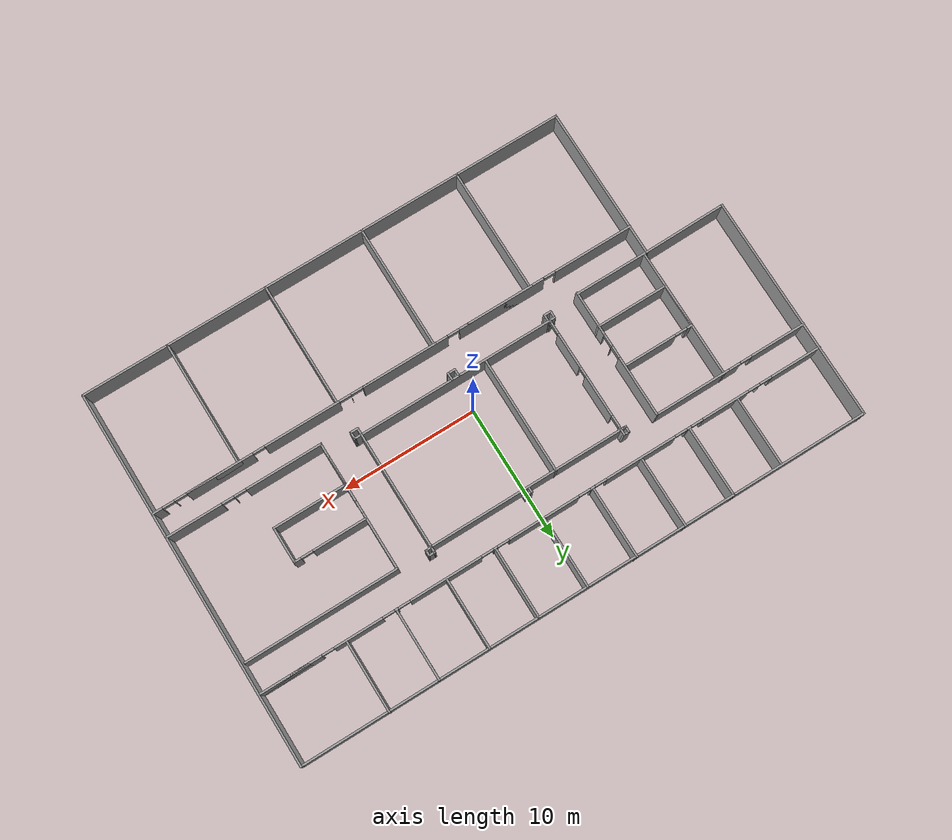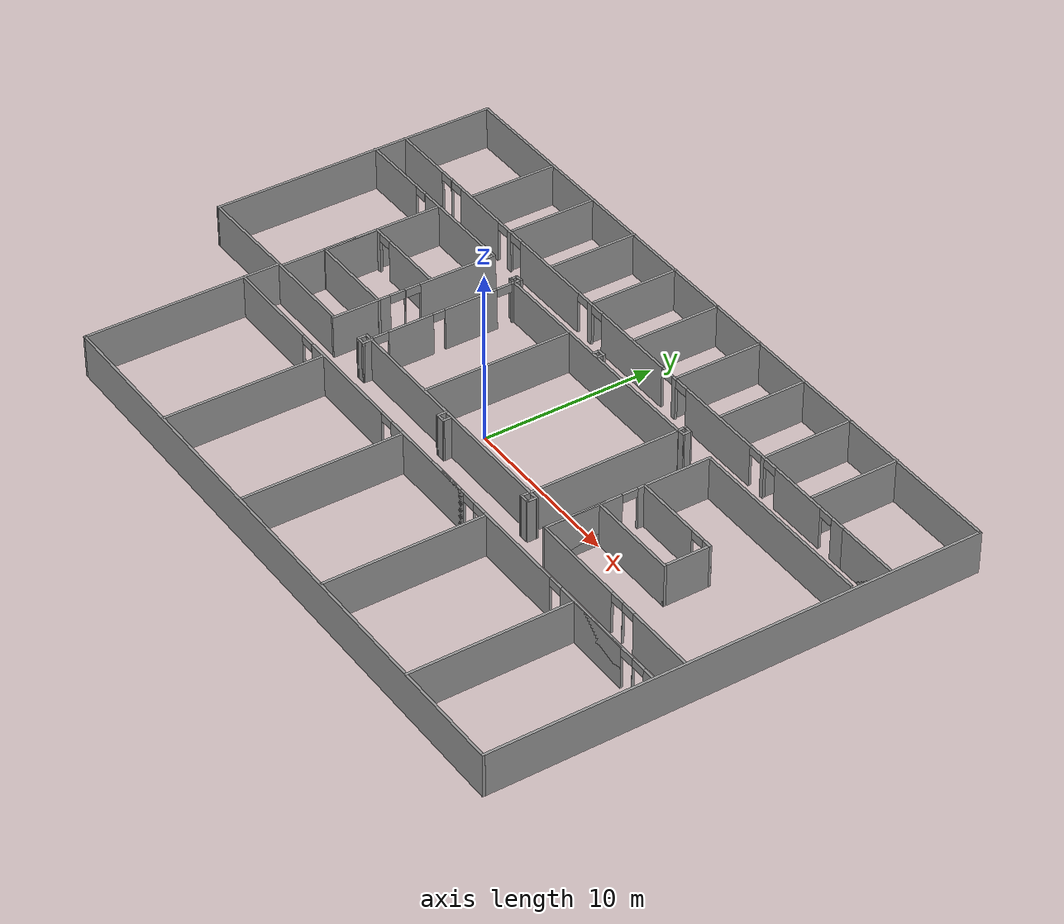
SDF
<?xml version='1.0'?>
<sdf version='1.7'>
  <model name='L8_4_gazebo'>
    <pose>-0.001511 -0.004516 0 0 -0 0</pose>
    <link name='Wall_0'>
      <collision name='Wall_0_Collision'>
        <geometry>
          <box>
            <size>43 0.15 2.5</size>
          </box>
        </geometry>
        <pose>0 0 1.25 0 -0 0</pose>
      </collision>
      <visual name='Wall_0_Visual'>
        <pose>0 0 1.25 0 -0 0</pose>
        <geometry>
          <box>
            <size>43 0.15 2.5</size>
          </box>
        </geometry>
        <material>
          <script>
            <uri>file://media/materials/scripts/gazebo.material</uri>
            <name>Gazebo/Grey</name>
          </script>
          <ambient>1 1 1 1</ambient>
        </material>
        <meta>
          <layer>0</layer>
        </meta>
      </visual>
      <pose>0.064696 14.0387 0 0 -0 0</pose>
    </link>
    <link name='Wall_1'>
      <collision name='Wall_1_Collision'>
        <geometry>
          <box>
            <size>28.25 0.15 2.5</size>
          </box>
        </geometry>
        <pose>0 0 1.25 0 -0 0</pose>
      </collision>
      <visual name='Wall_1_Visual'>
        <pose>0 0 1.25 0 -0 0</pose>
        <geometry>
          <box>
            <size>28.25 0.15 2.5</size>
          </box>
        </geometry>
        <material>
          <script>
            <uri>file://media/materials/scripts/gazebo.material</uri>
            <name>Gazebo/Grey</name>
          </script>
          <ambient>1 1 1 1</ambient>
        </material>
        <meta>
          <layer>0</layer>
        </meta>
      </visual>
      <pose>21.4897 -0.011288 0 0 -0 -1.5708</pose>
    </link>
    <link name='Wall_102'>
      <collision name='Wall_102_Collision'>
        <geometry>
          <box>
            <size>9.25 0.15 2.5</size>
          </box>
        </geometry>
        <pose>0 0 1.25 0 -0 0</pose>
      </collision>
      <visual name='Wall_102_Visual'>
        <pose>0 0 1.25 0 -0 0</pose>
        <geometry>
          <box>
            <size>9.25 0.15 2.5</size>
          </box>
        </geometry>
        <material>
          <script>
            <uri>file://media/materials/scripts/gazebo.material</uri>
            <name>Gazebo/Grey</name>
          </script>
          <ambient>1 1 1 1</ambient>
        </material>
        <meta>
          <layer>0</layer>
        </meta>
      </visual>
      <pose>15.0681 -9.50681 0 0 -0 1.5708</pose>
    </link>
    <link name='Wall_12'>
      <pose>-15.6834 6.94104 0 0 -0 0</pose>
      <visual name='Wall_12_Visual_0'>
        <pose>-3.77146 0 1.25 0 -0 0</pose>
        <geometry>
          <box>
            <size>4.20709 0.15 2.5</size>
          </box>
        </geometry>
        <material>
          <script>
            <uri>file://media/materials/scripts/gazebo.material</uri>
            <name>Gazebo/Grey</name>
          </script>
          <ambient>1 1 1 1</ambient>
        </material>
        <meta>
          <layer>0</layer>
        </meta>
      </visual>
      <collision name='Wall_12_Collision_0'>
        <geometry>
          <box>
            <size>4.20709 0.15 2.5</size>
          </box>
        </geometry>
        <pose>-3.77146 0 1.25 0 -0 0</pose>
      </collision>
      <visual name='Wall_12_Visual_1'>
        <pose>2.55355 0 1.25 0 -0 0</pose>
        <geometry>
          <box>
            <size>6.64291 0.15 2.5</size>
          </box>
        </geometry>
        <material>
          <script>
            <uri>file://media/materials/scripts/gazebo.material</uri>
            <name>Gazebo/Grey</name>
          </script>
          <ambient>1 1 1 1</ambient>
        </material>
        <meta>
          <layer>0</layer>
        </meta>
      </visual>
      <collision name='Wall_12_Collision_1'>
        <geometry>
          <box>
            <size>6.64291 0.15 2.5</size>
          </box>
        </geometry>
        <pose>2.55355 0 1.25 0 -0 0</pose>
      </collision>
      <visual name='Wall_12_Visual_2'>
        <pose>2.99355 0 1.25 0 -0 0</pose>
        <geometry>
          <box>
            <size>5.76291 0.15 2.5</size>
          </box>
        </geometry>
        <material>
          <script>
            <uri>file://media/materials/scripts/gazebo.material</uri>
            <name>Gazebo/Grey</name>
          </script>
          <ambient>1 1 1 1</ambient>
        </material>
        <meta>
          <layer>0</layer>
        </meta>
      </visual>
      <collision name='Wall_12_Collision_2'>
        <geometry>
          <box>
            <size>5.76291 0.15 2.5</size>
          </box>
        </geometry>
        <pose>2.99355 0 1.25 0 -0 0</pose>
      </collision>
      <visual name='Wall_12_Visual_3'>
        <pose>-1.22791 0 2.25 0 -0 0</pose>
        <geometry>
          <box>
            <size>0.880003 0.15 0.5</size>
          </box>
        </geometry>
        <material>
          <script>
            <uri>file://media/materials/scripts/gazebo.material</uri>
            <name>Gazebo/Grey</name>
          </script>
          <ambient>1 1 1 1</ambient>
        </material>
        <meta>
          <layer>0</layer>
        </meta>
      </visual>
      <collision name='Wall_12_Collision_3'>
        <geometry>
          <box>
            <size>0.880003 0.15 0.5</size>
          </box>
        </geometry>
        <pose>-1.22791 0 2.25 0 -0 0</pose>
      </collision>
    </link>
    <link name='Wall_13'>
      <pose>-9.88336 2.08119 0 0 -0 -1.5708</pose>
      <visual name='Wall_13_Visual_0'>
        <pose>-2.63558 0 1.25 0 -0 0</pose>
        <geometry>
          <box>
            <size>4.59855 0.15 2.5</size>
          </box>
        </geometry>
        <material>
          <script>
            <uri>file://media/materials/scripts/gazebo.material</uri>
            <name>Gazebo/Grey</name>
          </script>
          <ambient>1 1 1 1</ambient>
        </material>
        <meta>
          <layer>0</layer>
        </meta>
      </visual>
      <collision name='Wall_13_Collision_0'>
        <geometry>
          <box>
            <size>4.59855 0.15 2.5</size>
          </box>
        </geometry>
        <pose>-2.63558 0 1.25 0 -0 0</pose>
      </collision>
      <visual name='Wall_13_Visual_1'>
        <pose>0.576074 0 1.25 0 -0 0</pose>
        <geometry>
          <box>
            <size>0.024749 0.15 2.5</size>
          </box>
        </geometry>
        <material>
          <script>
            <uri>file://media/materials/scripts/gazebo.material</uri>
            <name>Gazebo/Grey</name>
          </script>
          <ambient>1 1 1 1</ambient>
        </material>
        <meta>
          <layer>0</layer>
        </meta>
      </visual>
      <collision name='Wall_13_Collision_1'>
        <geometry>
          <box>
            <size>0.024749 0.15 2.5</size>
          </box>
        </geometry>
        <pose>0.576074 0 1.25 0 -0 0</pose>
      </collision>
      <visual name='Wall_13_Visual_2'>
        <pose>3.21165 0 1.25 0 -0 0</pose>
        <geometry>
          <box>
            <size>3.4464 0.15 2.5</size>
          </box>
        </geometry>
        <material>
          <script>
            <uri>file://media/materials/scripts/gazebo.material</uri>
            <name>Gazebo/Grey</name>
          </script>
          <ambient>1 1 1 1</ambient>
        </material>
        <meta>
          <layer>0</layer>
        </meta>
      </visual>
      <collision name='Wall_13_Collision_2'>
        <geometry>
          <box>
            <size>3.4464 0.15 2.5</size>
          </box>
        </geometry>
        <pose>3.21165 0 1.25 0 -0 0</pose>
      </collision>
      <visual name='Wall_13_Visual_3'>
        <pose>0.113699 0 2.25 0 -0 0</pose>
        <geometry>
          <box>
            <size>0.9 0.15 0.5</size>
          </box>
        </geometry>
        <material>
          <script>
            <uri>file://media/materials/scripts/gazebo.material</uri>
            <name>Gazebo/Grey</name>
          </script>
          <ambient>1 1 1 1</ambient>
        </material>
        <meta>
          <layer>0</layer>
        </meta>
      </visual>
      <collision name='Wall_13_Collision_3'>
        <geometry>
          <box>
            <size>0.9 0.15 0.5</size>
          </box>
        </geometry>
        <pose>0.113699 0 2.25 0 -0 0</pose>
      </collision>
      <visual name='Wall_13_Visual_4'>
        <pose>1.03845 0 2.25 0 -0 0</pose>
        <geometry>
          <box>
            <size>0.9 0.15 0.5</size>
          </box>
        </geometry>
        <material>
          <script>
            <uri>file://media/materials/scripts/gazebo.material</uri>
            <name>Gazebo/Grey</name>
          </script>
          <ambient>1 1 1 1</ambient>
        </material>
        <meta>
          <layer>0</layer>
        </meta>
      </visual>
      <collision name='Wall_13_Collision_4'>
        <geometry>
          <box>
            <size>0.9 0.15 0.5</size>
          </box>
        </geometry>
        <pose>1.03845 0 2.25 0 -0 0</pose>
      </collision>
    </link>
    <link name='Wall_14'>
      <collision name='Wall_14_Collision'>
        <geometry>
          <box>
            <size>5.5 0.15 2.5</size>
          </box>
        </geometry>
        <pose>0 0 1.25 0 -0 0</pose>
      </collision>
      <visual name='Wall_14_Visual'>
        <pose>0 0 1.25 0 -0 0</pose>
        <geometry>
          <box>
            <size>5.5 0.15 2.5</size>
          </box>
        </geometry>
        <material>
          <script>
            <uri>file://media/materials/scripts/gazebo.material</uri>
            <name>Gazebo/Grey</name>
          </script>
          <ambient>1 1 1 1</ambient>
        </material>
        <meta>
          <layer>0</layer>
        </meta>
      </visual>
      <pose>-12.5584 -2.71881 0 0 -0 3.14159</pose>
    </link>
    <link name='Wall_16'>
      <collision name='Wall_16_Collision'>
        <geometry>
          <box>
            <size>11.5 0.15 2.5</size>
          </box>
        </geometry>
        <pose>0 0 1.25 0 -0 0</pose>
      </collision>
      <visual name='Wall_16_Visual'>
        <pose>0 0 1.25 0 -0 0</pose>
        <geometry>
          <box>
            <size>11.5 0.15 2.5</size>
          </box>
        </geometry>
        <material>
          <script>
            <uri>file://media/materials/scripts/gazebo.material</uri>
            <name>Gazebo/Grey</name>
          </script>
          <ambient>1 1 1 1</ambient>
        </material>
        <meta>
          <layer>0</layer>
        </meta>
      </visual>
      <pose>15.5346 6.59842 0 0 -0 3.14159</pose>
    </link>
    <link name='Wall_17'>
      <pose>9.85961 1.79842 0 0 -0 -1.5708</pose>
      <visual name='Wall_17_Visual_0'>
        <pose>-2.69913 0 1.25 0 -0 0</pose>
        <geometry>
          <box>
            <size>4.35173 0.15 2.5</size>
          </box>
        </geometry>
        <material>
          <script>
            <uri>file://media/materials/scripts/gazebo.material</uri>
            <name>Gazebo/Grey</name>
          </script>
          <ambient>1 1 1 1</ambient>
        </material>
        <meta>
          <layer>0</layer>
        </meta>
      </visual>
      <collision name='Wall_17_Collision_0'>
        <geometry>
          <box>
            <size>4.35173 0.15 2.5</size>
          </box>
        </geometry>
        <pose>-2.69913 0 1.25 0 -0 0</pose>
      </collision>
      <visual name='Wall_17_Visual_1'>
        <pose>2.62587 0 1.25 0 -0 0</pose>
        <geometry>
          <box>
            <size>4.49827 0.15 2.5</size>
          </box>
        </geometry>
        <material>
          <script>
            <uri>file://media/materials/scripts/gazebo.material</uri>
            <name>Gazebo/Grey</name>
          </script>
          <ambient>1 1 1 1</ambient>
        </material>
        <meta>
          <layer>0</layer>
        </meta>
      </visual>
      <collision name='Wall_17_Collision_1'>
        <geometry>
          <box>
            <size>4.49827 0.15 2.5</size>
          </box>
        </geometry>
        <pose>2.62587 0 1.25 0 -0 0</pose>
      </collision>
      <visual name='Wall_17_Visual_2'>
        <pose>3.06821 0 1.25 0 -0 0</pose>
        <geometry>
          <box>
            <size>3.61358 0.15 2.5</size>
          </box>
        </geometry>
        <material>
          <script>
            <uri>file://media/materials/scripts/gazebo.material</uri>
            <name>Gazebo/Grey</name>
          </script>
          <ambient>1 1 1 1</ambient>
        </material>
        <meta>
          <layer>0</layer>
        </meta>
      </visual>
      <collision name='Wall_17_Collision_2'>
        <geometry>
          <box>
            <size>3.61358 0.15 2.5</size>
          </box>
        </geometry>
        <pose>3.06821 0 1.25 0 -0 0</pose>
      </collision>
      <visual name='Wall_17_Visual_3'>
        <pose>-0.080923 0 2.25 0 -0 0</pose>
        <geometry>
          <box>
            <size>0.884688 0.15 0.5</size>
          </box>
        </geometry>
        <material>
          <script>
            <uri>file://media/materials/scripts/gazebo.material</uri>
            <name>Gazebo/Grey</name>
          </script>
          <ambient>1 1 1 1</ambient>
        </material>
        <meta>
          <layer>0</layer>
        </meta>
      </visual>
      <collision name='Wall_17_Collision_3'>
        <geometry>
          <box>
            <size>0.884688 0.15 0.5</size>
          </box>
        </geometry>
        <pose>-0.080923 0 2.25 0 -0 0</pose>
      </collision>
    </link>
    <link name='Wall_18'>
      <pose>15.6596 -3.00158 0 0 -0 0</pose>
      <visual name='Wall_18_Visual_0'>
        <pose>-3.00399 0 1.25 0 -0 0</pose>
        <geometry>
          <box>
            <size>5.74203 0.15 2.5</size>
          </box>
        </geometry>
        <material>
          <script>
            <uri>file://media/materials/scripts/gazebo.material</uri>
            <name>Gazebo/Grey</name>
          </script>
          <ambient>1 1 1 1</ambient>
        </material>
        <meta>
          <layer>0</layer>
        </meta>
      </visual>
      <collision name='Wall_18_Collision_0'>
        <geometry>
          <box>
            <size>5.74203 0.15 2.5</size>
          </box>
        </geometry>
        <pose>-3.00399 0 1.25 0 -0 0</pose>
      </collision>
      <visual name='Wall_18_Visual_1'>
        <pose>0.770714 0 1.25 0 -0 0</pose>
        <geometry>
          <box>
            <size>0.007373 0.15 2.5</size>
          </box>
        </geometry>
        <material>
          <script>
            <uri>file://media/materials/scripts/gazebo.material</uri>
            <name>Gazebo/Grey</name>
          </script>
          <ambient>1 1 1 1</ambient>
        </material>
        <meta>
          <layer>0</layer>
        </meta>
      </visual>
      <collision name='Wall_18_Collision_1'>
        <geometry>
          <box>
            <size>0.007373 0.15 2.5</size>
          </box>
        </geometry>
        <pose>0.770714 0 1.25 0 -0 0</pose>
      </collision>
      <visual name='Wall_18_Visual_2'>
        <pose>3.7747 0 1.25 0 -0 0</pose>
        <geometry>
          <box>
            <size>4.2006 0.15 2.5</size>
          </box>
        </geometry>
        <material>
          <script>
            <uri>file://media/materials/scripts/gazebo.material</uri>
            <name>Gazebo/Grey</name>
          </script>
          <ambient>1 1 1 1</ambient>
        </material>
        <meta>
          <layer>0</layer>
        </meta>
      </visual>
      <collision name='Wall_18_Collision_2'>
        <geometry>
          <box>
            <size>4.2006 0.15 2.5</size>
          </box>
        </geometry>
        <pose>3.7747 0 1.25 0 -0 0</pose>
      </collision>
      <visual name='Wall_18_Visual_3'>
        <pose>0.317027 0 2.25 0 -0 0</pose>
        <geometry>
          <box>
            <size>0.9 0.15 0.5</size>
          </box>
        </geometry>
        <material>
          <script>
            <uri>file://media/materials/scripts/gazebo.material</uri>
            <name>Gazebo/Grey</name>
          </script>
          <ambient>1 1 1 1</ambient>
        </material>
        <meta>
          <layer>0</layer>
        </meta>
      </visual>
      <collision name='Wall_18_Collision_3'>
        <geometry>
          <box>
            <size>0.9 0.15 0.5</size>
          </box>
        </geometry>
        <pose>0.317027 0 2.25 0 -0 0</pose>
      </collision>
      <visual name='Wall_18_Visual_4'>
        <pose>1.2244 0 2.25 0 -0 0</pose>
        <geometry>
          <box>
            <size>0.9 0.15 0.5</size>
          </box>
        </geometry>
        <material>
          <script>
            <uri>file://media/materials/scripts/gazebo.material</uri>
            <name>Gazebo/Grey</name>
          </script>
          <ambient>1 1 1 1</ambient>
        </material>
        <meta>
          <layer>0</layer>
        </meta>
      </visual>
      <collision name='Wall_18_Collision_4'>
        <geometry>
          <box>
            <size>0.9 0.15 0.5</size>
          </box>
        </geometry>
        <pose>1.2244 0 2.25 0 -0 0</pose>
      </collision>
    </link>
    <link name='Wall_2'>
      <collision name='Wall_2_Collision'>
        <geometry>
          <box>
            <size>37 0.15 2.5</size>
          </box>
        </geometry>
        <pose>0 0 1.25 0 -0 0</pose>
      </collision>
      <visual name='Wall_2_Visual'>
        <pose>0 0 1.25 0 -0 0</pose>
        <geometry>
          <box>
            <size>37 0.15 2.5</size>
          </box>
        </geometry>
        <material>
          <script>
            <uri>file://media/materials/scripts/gazebo.material</uri>
            <name>Gazebo/Grey</name>
          </script>
          <ambient>1 1 1 1</ambient>
        </material>
        <meta>
          <layer>0</layer>
        </meta>
      </visual>
      <pose>3.0647 -14.0613 0 0 -0 3.14159</pose>
    </link>
    <link name='Wall_20'>
      <pose>3.04545 -4.80901 0 0 -0 0</pose>
      <visual name='Wall_20_Visual_0'>
        <pose>-15.485 0 1.25 0 -0 0</pose>
        <geometry>
          <box>
            <size>6.02996 0.15 2.5</size>
          </box>
        </geometry>
        <material>
          <script>
            <uri>file://media/materials/scripts/gazebo.material</uri>
            <name>Gazebo/Grey</name>
          </script>
          <ambient>1 1 1 1</ambient>
        </material>
        <meta>
          <layer>0</layer>
        </meta>
      </visual>
      <collision name='Wall_20_Collision_0'>
        <geometry>
          <box>
            <size>6.02996 0.15 2.5</size>
          </box>
        </geometry>
        <pose>-15.485 0 1.25 0 -0 0</pose>
      </collision>
      <visual name='Wall_20_Visual_1'>
        <pose>-8.25445 0 1.25 0 -0 0</pose>
        <geometry>
          <box>
            <size>6.63119 0.15 2.5</size>
          </box>
        </geometry>
        <material>
          <script>
            <uri>file://media/materials/scripts/gazebo.material</uri>
            <name>Gazebo/Grey</name>
          </script>
          <ambient>1 1 1 1</ambient>
        </material>
        <meta>
          <layer>0</layer>
        </meta>
      </visual>
      <collision name='Wall_20_Collision_1'>
        <geometry>
          <box>
            <size>6.63119 0.15 2.5</size>
          </box>
        </geometry>
        <pose>-8.25445 0 1.25 0 -0 0</pose>
      </collision>
      <visual name='Wall_20_Visual_2'>
        <pose>-7.8121 0 1.25 0 -0 0</pose>
        <geometry>
          <box>
            <size>5.7465 0.15 2.5</size>
          </box>
        </geometry>
        <material>
          <script>
            <uri>file://media/materials/scripts/gazebo.material</uri>
            <name>Gazebo/Grey</name>
          </script>
          <ambient>1 1 1 1</ambient>
        </material>
        <meta>
          <layer>0</layer>
        </meta>
      </visual>
      <collision name='Wall_20_Collision_2'>
        <geometry>
          <box>
            <size>5.7465 0.15 2.5</size>
          </box>
        </geometry>
        <pose>-7.8121 0 1.25 0 -0 0</pose>
      </collision>
      <visual name='Wall_20_Visual_3'>
        <pose>-0.757283 0 1.25 0 -0 0</pose>
        <geometry>
          <box>
            <size>6.56314 0.15 2.5</size>
          </box>
        </geometry>
        <material>
          <script>
            <uri>file://media/materials/scripts/gazebo.material</uri>
            <name>Gazebo/Grey</name>
          </script>
          <ambient>1 1 1 1</ambient>
        </material>
        <meta>
          <layer>0</layer>
        </meta>
      </visual>
      <collision name='Wall_20_Collision_3'>
        <geometry>
          <box>
            <size>6.56314 0.15 2.5</size>
          </box>
        </geometry>
        <pose>-0.757283 0 1.25 0 -0 0</pose>
      </collision>
      <visual name='Wall_20_Visual_4'>
        <pose>-0.314939 0 1.25 0 -0 0</pose>
        <geometry>
          <box>
            <size>5.67845 0.15 2.5</size>
          </box>
        </geometry>
        <material>
          <script>
            <uri>file://media/materials/scripts/gazebo.material</uri>
            <name>Gazebo/Grey</name>
          </script>
          <ambient>1 1 1 1</ambient>
        </material>
        <meta>
          <layer>0</layer>
        </meta>
      </visual>
      <collision name='Wall_20_Collision_4'>
        <geometry>
          <box>
            <size>5.67845 0.15 2.5</size>
          </box>
        </geometry>
        <pose>-0.314939 0 1.25 0 -0 0</pose>
      </collision>
      <visual name='Wall_20_Visual_5'>
        <pose>3.42797 0 1.25 0 -0 0</pose>
        <geometry>
          <box>
            <size>0.007372 0.15 2.5</size>
          </box>
        </geometry>
        <material>
          <script>
            <uri>file://media/materials/scripts/gazebo.material</uri>
            <name>Gazebo/Grey</name>
          </script>
          <ambient>1 1 1 1</ambient>
        </material>
        <meta>
          <layer>0</layer>
        </meta>
      </visual>
      <collision name='Wall_20_Collision_5'>
        <geometry>
          <box>
            <size>0.007372 0.15 2.5</size>
          </box>
        </geometry>
        <pose>3.42797 0 1.25 0 -0 0</pose>
      </collision>
      <visual name='Wall_20_Visual_6'>
        <pose>7.17088 0 1.25 0 -0 0</pose>
        <geometry>
          <box>
            <size>5.67845 0.15 2.5</size>
          </box>
        </geometry>
        <material>
          <script>
            <uri>file://media/materials/scripts/gazebo.material</uri>
            <name>Gazebo/Grey</name>
          </script>
          <ambient>1 1 1 1</ambient>
        </material>
        <meta>
          <layer>0</layer>
        </meta>
      </visual>
      <collision name='Wall_20_Collision_6'>
        <geometry>
          <box>
            <size>5.67845 0.15 2.5</size>
          </box>
        </geometry>
        <pose>7.17088 0 1.25 0 -0 0</pose>
      </collision>
      <visual name='Wall_20_Visual_7'>
        <pose>13.4091 0 1.25 0 -0 0</pose>
        <geometry>
          <box>
            <size>4.99792 0.15 2.5</size>
          </box>
        </geometry>
        <material>
          <script>
            <uri>file://media/materials/scripts/gazebo.material</uri>
            <name>Gazebo/Grey</name>
          </script>
          <ambient>1 1 1 1</ambient>
        </material>
        <meta>
          <layer>0</layer>
        </meta>
      </visual>
      <collision name='Wall_20_Collision_7'>
        <geometry>
          <box>
            <size>4.99792 0.15 2.5</size>
          </box>
        </geometry>
        <pose>13.4091 0 1.25 0 -0 0</pose>
      </collision>
      <visual name='Wall_20_Visual_8'>
        <pose>13.8514 0 1.25 0 -0 0</pose>
        <geometry>
          <box>
            <size>4.11323 0.15 2.5</size>
          </box>
        </geometry>
        <material>
          <script>
            <uri>file://media/materials/scripts/gazebo.material</uri>
            <name>Gazebo/Grey</name>
          </script>
          <ambient>1 1 1 1</ambient>
        </material>
        <meta>
          <layer>0</layer>
        </meta>
      </visual>
      <collision name='Wall_20_Collision_8'>
        <geometry>
          <box>
            <size>4.11323 0.15 2.5</size>
          </box>
        </geometry>
        <pose>13.8514 0 1.25 0 -0 0</pose>
      </collision>
      <visual name='Wall_20_Visual_9'>
        <pose>16.8117 0 1.25 0 -0 0</pose>
        <geometry>
          <box>
            <size>0.007373 0.15 2.5</size>
          </box>
        </geometry>
        <material>
          <script>
            <uri>file://media/materials/scripts/gazebo.material</uri>
            <name>Gazebo/Grey</name>
          </script>
          <ambient>1 1 1 1</ambient>
        </material>
        <meta>
          <layer>0</layer>
        </meta>
      </visual>
      <collision name='Wall_20_Collision_9'>
        <geometry>
          <box>
            <size>0.007373 0.15 2.5</size>
          </box>
        </geometry>
        <pose>16.8117 0 1.25 0 -0 0</pose>
      </collision>
      <visual name='Wall_20_Visual_10'>
        <pose>18.1077 0 1.25 0 -0 0</pose>
        <geometry>
          <box>
            <size>0.784598 0.15 2.5</size>
          </box>
        </geometry>
        <material>
          <script>
            <uri>file://media/materials/scripts/gazebo.material</uri>
            <name>Gazebo/Grey</name>
          </script>
          <ambient>1 1 1 1</ambient>
        </material>
        <meta>
          <layer>0</layer>
        </meta>
      </visual>
      <collision name='Wall_20_Collision_10'>
        <geometry>
          <box>
            <size>0.784598 0.15 2.5</size>
          </box>
        </geometry>
        <pose>18.1077 0 1.25 0 -0 0</pose>
      </collision>
      <visual name='Wall_20_Visual_11'>
        <pose>-12.0277 0 2.25 0 -0 0</pose>
        <geometry>
          <box>
            <size>0.884688 0.15 0.5</size>
          </box>
        </geometry>
        <material>
          <script>
            <uri>file://media/materials/scripts/gazebo.material</uri>
            <name>Gazebo/Grey</name>
          </script>
          <ambient>1 1 1 1</ambient>
        </material>
        <meta>
          <layer>0</layer>
        </meta>
      </visual>
      <collision name='Wall_20_Collision_11'>
        <geometry>
          <box>
            <size>0.884688 0.15 0.5</size>
          </box>
        </geometry>
        <pose>-12.0277 0 2.25 0 -0 0</pose>
      </collision>
      <visual name='Wall_20_Visual_12'>
        <pose>-4.49651 0 2.25 0 -0 0</pose>
        <geometry>
          <box>
            <size>0.884688 0.15 0.5</size>
          </box>
        </geometry>
        <material>
          <script>
            <uri>file://media/materials/scripts/gazebo.material</uri>
            <name>Gazebo/Grey</name>
          </script>
          <ambient>1 1 1 1</ambient>
        </material>
        <meta>
          <layer>0</layer>
        </meta>
      </visual>
      <collision name='Wall_20_Collision_12'>
        <geometry>
          <box>
            <size>0.884688 0.15 0.5</size>
          </box>
        </geometry>
        <pose>-4.49651 0 2.25 0 -0 0</pose>
      </collision>
      <visual name='Wall_20_Visual_13'>
        <pose>-4.49651 0 2.25 0 -0 0</pose>
        <geometry>
          <box>
            <size>0.884688 0.15 0.5</size>
          </box>
        </geometry>
        <material>
          <script>
            <uri>file://media/materials/scripts/gazebo.material</uri>
            <name>Gazebo/Grey</name>
          </script>
          <ambient>1 1 1 1</ambient>
        </material>
        <meta>
          <layer>0</layer>
        </meta>
      </visual>
      <collision name='Wall_20_Collision_13'>
        <geometry>
          <box>
            <size>0.884688 0.15 0.5</size>
          </box>
        </geometry>
        <pose>-4.49651 0 2.25 0 -0 0</pose>
      </collision>
      <visual name='Wall_20_Visual_14'>
        <pose>2.97429 0 2.25 0 -0 0</pose>
        <geometry>
          <box>
            <size>0.9 0.15 0.5</size>
          </box>
        </geometry>
        <material>
          <script>
            <uri>file://media/materials/scripts/gazebo.material</uri>
            <name>Gazebo/Grey</name>
          </script>
          <ambient>1 1 1 1</ambient>
        </material>
        <meta>
          <layer>0</layer>
        </meta>
      </visual>
      <collision name='Wall_20_Collision_14'>
        <geometry>
          <box>
            <size>0.9 0.15 0.5</size>
          </box>
        </geometry>
        <pose>2.97429 0 2.25 0 -0 0</pose>
      </collision>
      <visual name='Wall_20_Visual_15'>
        <pose>2.97429 0 2.25 0 -0 0</pose>
        <geometry>
          <box>
            <size>0.9 0.15 0.5</size>
          </box>
        </geometry>
        <material>
          <script>
            <uri>file://media/materials/scripts/gazebo.material</uri>
            <name>Gazebo/Grey</name>
          </script>
          <ambient>1 1 1 1</ambient>
        </material>
        <meta>
          <layer>0</layer>
        </meta>
      </visual>
      <collision name='Wall_20_Collision_15'>
        <geometry>
          <box>
            <size>0.9 0.15 0.5</size>
          </box>
        </geometry>
        <pose>2.97429 0 2.25 0 -0 0</pose>
      </collision>
      <visual name='Wall_20_Visual_16'>
        <pose>3.88166 0 2.25 0 -0 0</pose>
        <geometry>
          <box>
            <size>0.9 0.15 0.5</size>
          </box>
        </geometry>
        <material>
          <script>
            <uri>file://media/materials/scripts/gazebo.material</uri>
            <name>Gazebo/Grey</name>
          </script>
          <ambient>1 1 1 1</ambient>
        </material>
        <meta>
          <layer>0</layer>
        </meta>
      </visual>
      <collision name='Wall_20_Collision_16'>
        <geometry>
          <box>
            <size>0.9 0.15 0.5</size>
          </box>
        </geometry>
        <pose>3.88166 0 2.25 0 -0 0</pose>
      </collision>
      <visual name='Wall_20_Visual_17'>
        <pose>10.4525 0 2.25 0 -0 0</pose>
        <geometry>
          <box>
            <size>0.884688 0.15 0.5</size>
          </box>
        </geometry>
        <material>
          <script>
            <uri>file://media/materials/scripts/gazebo.material</uri>
            <name>Gazebo/Grey</name>
          </script>
          <ambient>1 1 1 1</ambient>
        </material>
        <meta>
          <layer>0</layer>
        </meta>
      </visual>
      <collision name='Wall_20_Collision_17'>
        <geometry>
          <box>
            <size>0.884688 0.15 0.5</size>
          </box>
        </geometry>
        <pose>10.4525 0 2.25 0 -0 0</pose>
      </collision>
      <visual name='Wall_20_Visual_18'>
        <pose>16.358 0 2.25 0 -0 0</pose>
        <geometry>
          <box>
            <size>0.9 0.15 0.5</size>
          </box>
        </geometry>
        <material>
          <script>
            <uri>file://media/materials/scripts/gazebo.material</uri>
            <name>Gazebo/Grey</name>
          </script>
          <ambient>1 1 1 1</ambient>
        </material>
        <meta>
          <layer>0</layer>
        </meta>
      </visual>
      <collision name='Wall_20_Collision_18'>
        <geometry>
          <box>
            <size>0.9 0.15 0.5</size>
          </box>
        </geometry>
        <pose>16.358 0 2.25 0 -0 0</pose>
      </collision>
      <visual name='Wall_20_Visual_19'>
        <pose>16.358 0 2.25 0 -0 0</pose>
        <geometry>
          <box>
            <size>0.9 0.15 0.5</size>
          </box>
        </geometry>
        <material>
          <script>
            <uri>file://media/materials/scripts/gazebo.material</uri>
            <name>Gazebo/Grey</name>
          </script>
          <ambient>1 1 1 1</ambient>
        </material>
        <meta>
          <layer>0</layer>
        </meta>
      </visual>
      <collision name='Wall_20_Collision_19'>
        <geometry>
          <box>
            <size>0.9 0.15 0.5</size>
          </box>
        </geometry>
        <pose>16.358 0 2.25 0 -0 0</pose>
      </collision>
      <visual name='Wall_20_Visual_20'>
        <pose>17.2654 0 2.25 0 -0 0</pose>
        <geometry>
          <box>
            <size>0.9 0.15 0.5</size>
          </box>
        </geometry>
        <material>
          <script>
            <uri>file://media/materials/scripts/gazebo.material</uri>
            <name>Gazebo/Grey</name>
          </script>
          <ambient>1 1 1 1</ambient>
        </material>
        <meta>
          <layer>0</layer>
        </meta>
      </visual>
      <collision name='Wall_20_Collision_20'>
        <geometry>
          <box>
            <size>0.9 0.15 0.5</size>
          </box>
        </geometry>
        <pose>17.2654 0 2.25 0 -0 0</pose>
      </collision>
    </link>
    <link name='Wall_27'>
      <collision name='Wall_27_Collision'>
        <geometry>
          <box>
            <size>0.511591 0.15 2.5</size>
          </box>
        </geometry>
        <pose>0 0 1.25 0 -0 0</pose>
      </collision>
      <visual name='Wall_27_Visual'>
        <pose>0 0 1.25 0 -0 0</pose>
        <geometry>
          <box>
            <size>0.511591 0.15 2.5</size>
          </box>
        </geometry>
        <material>
          <script>
            <uri>file://media/materials/scripts/gazebo.material</uri>
            <name>Gazebo/Grey</name>
          </script>
          <ambient>1 1 1 1</ambient>
        </material>
        <meta>
          <layer>0</layer>
        </meta>
      </visual>
      <pose>-7.33568 6.74149 0 0 -0 1.5708</pose>
    </link>
    <link name='Wall_28'>
      <collision name='Wall_28_Collision'>
        <geometry>
          <box>
            <size>0.5 0.15 2.5</size>
          </box>
        </geometry>
        <pose>0 0 1.25 0 -0 0</pose>
      </collision>
      <visual name='Wall_28_Visual'>
        <pose>0 0 1.25 0 -0 0</pose>
        <geometry>
          <box>
            <size>0.5 0.15 2.5</size>
          </box>
        </geometry>
        <material>
          <script>
            <uri>file://media/materials/scripts/gazebo.material</uri>
            <name>Gazebo/Grey</name>
          </script>
          <ambient>1 1 1 1</ambient>
        </material>
        <meta>
          <layer>0</layer>
        </meta>
      </visual>
      <pose>-7.51068 6.92604 0 0 -0 3.14159</pose>
    </link>
    <link name='Wall_29'>
      <collision name='Wall_29_Collision'>
        <geometry>
          <box>
            <size>0.528824 0.15 2.5</size>
          </box>
        </geometry>
        <pose>0 0 1.25 0 -0 0</pose>
      </collision>
      <visual name='Wall_29_Visual'>
        <pose>0 0 1.25 0 -0 0</pose>
        <geometry>
          <box>
            <size>0.528824 0.15 2.5</size>
          </box>
        </geometry>
        <material>
          <script>
            <uri>file://media/materials/scripts/gazebo.material</uri>
            <name>Gazebo/Grey</name>
          </script>
          <ambient>1 1 1 1</ambient>
        </material>
        <meta>
          <layer>0</layer>
        </meta>
      </visual>
      <pose>-7.68943 6.73291 0 0 -0 -1.5906</pose>
    </link>
    <link name='Wall_3'>
      <collision name='Wall_3_Collision'>
        <geometry>
          <box>
            <size>11.5 0.15 2.5</size>
          </box>
        </geometry>
        <pose>0 0 1.25 0 -0 0</pose>
      </collision>
      <visual name='Wall_3_Visual'>
        <pose>0 0 1.25 0 -0 0</pose>
        <geometry>
          <box>
            <size>11.5 0.15 2.5</size>
          </box>
        </geometry>
        <material>
          <script>
            <uri>file://media/materials/scripts/gazebo.material</uri>
            <name>Gazebo/Grey</name>
          </script>
          <ambient>1 1 1 1</ambient>
        </material>
        <meta>
          <layer>0</layer>
        </meta>
      </visual>
      <pose>-15.3603 -8.38629 0 0 -0 1.5708</pose>
    </link>
    <link name='Wall_30'>
      <collision name='Wall_30_Collision'>
        <geometry>
          <box>
            <size>0.5 0.15 2.5</size>
          </box>
        </geometry>
        <pose>0 0 1.25 0 -0 0</pose>
      </collision>
      <visual name='Wall_30_Visual'>
        <pose>0 0 1.25 0 -0 0</pose>
        <geometry>
          <box>
            <size>0.5 0.15 2.5</size>
          </box>
        </geometry>
        <material>
          <script>
            <uri>file://media/materials/scripts/gazebo.material</uri>
            <name>Gazebo/Grey</name>
          </script>
          <ambient>1 1 1 1</ambient>
        </material>
        <meta>
          <layer>0</layer>
        </meta>
      </visual>
      <pose>-7.51818 6.54354 0 0 -0 0</pose>
    </link>
    <link name='Wall_31'>
      <collision name='Wall_31_Collision'>
        <geometry>
          <box>
            <size>0.5 0.15 2.5</size>
          </box>
        </geometry>
        <pose>0 0 1.25 0 -0 0</pose>
      </collision>
      <visual name='Wall_31_Visual'>
        <pose>0 0 1.25 0 -0 0</pose>
        <geometry>
          <box>
            <size>0.5 0.15 2.5</size>
          </box>
        </geometry>
        <material>
          <script>
            <uri>file://media/materials/scripts/gazebo.material</uri>
            <name>Gazebo/Grey</name>
          </script>
          <ambient>1 1 1 1</ambient>
        </material>
        <meta>
          <layer>0</layer>
        </meta>
      </visual>
      <pose>-7.51818 6.54354 0 0 -0 3.14159</pose>
    </link>
    <link name='Wall_32'>
      <collision name='Wall_32_Collision'>
        <geometry>
          <box>
            <size>0.5 0.15 2.5</size>
          </box>
        </geometry>
        <pose>0 0 1.25 0 -0 0</pose>
      </collision>
      <visual name='Wall_32_Visual'>
        <pose>0 0 1.25 0 -0 0</pose>
        <geometry>
          <box>
            <size>0.5 0.15 2.5</size>
          </box>
        </geometry>
        <material>
          <script>
            <uri>file://media/materials/scripts/gazebo.material</uri>
            <name>Gazebo/Grey</name>
          </script>
          <ambient>1 1 1 1</ambient>
        </material>
        <meta>
          <layer>0</layer>
        </meta>
      </visual>
      <pose>-7.51443 6.53979 0 0 -0 0</pose>
    </link>
    <link name='Wall_34'>
      <collision name='Wall_34_Collision'>
        <geometry>
          <box>
            <size>0.461188 0.15 2.5</size>
          </box>
        </geometry>
        <pose>0 0 1.25 0 -0 0</pose>
      </collision>
      <visual name='Wall_34_Visual'>
        <pose>0 0 1.25 0 -0 0</pose>
        <geometry>
          <box>
            <size>0.461188 0.15 2.5</size>
          </box>
        </geometry>
        <material>
          <script>
            <uri>file://media/materials/scripts/gazebo.material</uri>
            <name>Gazebo/Grey</name>
          </script>
          <ambient>1 1 1 1</ambient>
        </material>
        <meta>
          <layer>0</layer>
        </meta>
      </visual>
      <pose>-0.156622 6.77306 0 0 -0 1.5708</pose>
    </link>
    <link name='Wall_35'>
      <collision name='Wall_35_Collision'>
        <geometry>
          <box>
            <size>0.543 0.15 2.5</size>
          </box>
        </geometry>
        <pose>0 0 1.25 0 -0 0</pose>
      </collision>
      <visual name='Wall_35_Visual'>
        <pose>0 0 1.25 0 -0 0</pose>
        <geometry>
          <box>
            <size>0.543 0.15 2.5</size>
          </box>
        </geometry>
        <material>
          <script>
            <uri>file://media/materials/scripts/gazebo.material</uri>
            <name>Gazebo/Grey</name>
          </script>
          <ambient>1 1 1 1</ambient>
        </material>
        <meta>
          <layer>0</layer>
        </meta>
      </visual>
      <pose>0.039878 6.92434 0 0 -0 0</pose>
    </link>
    <link name='Wall_36'>
      <collision name='Wall_36_Collision'>
        <geometry>
          <box>
            <size>0.461188 0.15 2.5</size>
          </box>
        </geometry>
        <pose>0 0 1.25 0 -0 0</pose>
      </collision>
      <visual name='Wall_36_Visual'>
        <pose>0 0 1.25 0 -0 0</pose>
        <geometry>
          <box>
            <size>0.461188 0.15 2.5</size>
          </box>
        </geometry>
        <material>
          <script>
            <uri>file://media/materials/scripts/gazebo.material</uri>
            <name>Gazebo/Grey</name>
          </script>
          <ambient>1 1 1 1</ambient>
        </material>
        <meta>
          <layer>0</layer>
        </meta>
      </visual>
      <pose>0.236378 6.77306 0 0 -0 -1.5708</pose>
    </link>
    <link name='Wall_38'>
      <collision name='Wall_38_Collision'>
        <geometry>
          <box>
            <size>0.560618 0.15 2.5</size>
          </box>
        </geometry>
        <pose>0 0 1.25 0 -0 0</pose>
      </collision>
      <visual name='Wall_38_Visual'>
        <pose>0 0 1.25 0 -0 0</pose>
        <geometry>
          <box>
            <size>0.560618 0.15 2.5</size>
          </box>
        </geometry>
        <material>
          <script>
            <uri>file://media/materials/scripts/gazebo.material</uri>
            <name>Gazebo/Grey</name>
          </script>
          <ambient>1 1 1 1</ambient>
        </material>
        <meta>
          <layer>0</layer>
        </meta>
      </visual>
      <pose>7.27186 6.76587 0 0 -0 1.60754</pose>
    </link>
    <link name='Wall_39'>
      <collision name='Wall_39_Collision'>
        <geometry>
          <box>
            <size>0.547461 0.15 2.5</size>
          </box>
        </geometry>
        <pose>0 0 1.25 0 -0 0</pose>
      </collision>
      <visual name='Wall_39_Visual'>
        <pose>0 0 1.25 0 -0 0</pose>
        <geometry>
          <box>
            <size>0.547461 0.15 2.5</size>
          </box>
        </geometry>
        <material>
          <script>
            <uri>file://media/materials/scripts/gazebo.material</uri>
            <name>Gazebo/Grey</name>
          </script>
          <ambient>1 1 1 1</ambient>
        </material>
        <meta>
          <layer>0</layer>
        </meta>
      </visual>
      <pose>7.46304 6.96888 0 0 -0 -0.01085</pose>
    </link>
    <link name='Wall_4'>
      <collision name='Wall_4_Collision'>
        <geometry>
          <box>
            <size>6.25 0.15 2.5</size>
          </box>
        </geometry>
        <pose>0 0 1.25 0 -0 0</pose>
      </collision>
      <visual name='Wall_4_Visual'>
        <pose>0 0 1.25 0 -0 0</pose>
        <geometry>
          <box>
            <size>6.25 0.15 2.5</size>
          </box>
        </geometry>
        <material>
          <script>
            <uri>file://media/materials/scripts/gazebo.material</uri>
            <name>Gazebo/Grey</name>
          </script>
          <ambient>1 1 1 1</ambient>
        </material>
        <meta>
          <layer>0</layer>
        </meta>
      </visual>
      <pose>-18.4103 -2.7502 0 0 -0 -3.12884</pose>
    </link>
    <link name='Wall_40'>
      <collision name='Wall_40_Collision'>
        <geometry>
          <box>
            <size>0.51725 0.15 2.5</size>
          </box>
        </geometry>
        <pose>0 0 1.25 0 -0 0</pose>
      </collision>
      <visual name='Wall_40_Visual'>
        <pose>0 0 1.25 0 -0 0</pose>
        <geometry>
          <box>
            <size>0.51725 0.15 2.5</size>
          </box>
        </geometry>
        <material>
          <script>
            <uri>file://media/materials/scripts/gazebo.material</uri>
            <name>Gazebo/Grey</name>
          </script>
          <ambient>1 1 1 1</ambient>
        </material>
        <meta>
          <layer>0</layer>
        </meta>
      </visual>
      <pose>7.66176 6.7831 0 0 -0 -1.5708</pose>
    </link>
    <link name='Wall_41'>
      <collision name='Wall_41_Collision'>
        <geometry>
          <box>
            <size>0.533903 0.15 2.5</size>
          </box>
        </geometry>
        <pose>0 0 1.25 0 -0 0</pose>
      </collision>
      <visual name='Wall_41_Visual'>
        <pose>0 0 1.25 0 -0 0</pose>
        <geometry>
          <box>
            <size>0.533903 0.15 2.5</size>
          </box>
        </geometry>
        <material>
          <script>
            <uri>file://media/materials/scripts/gazebo.material</uri>
            <name>Gazebo/Grey</name>
          </script>
          <ambient>1 1 1 1</ambient>
        </material>
        <meta>
          <layer>0</layer>
        </meta>
      </visual>
      <pose>7.47058 6.57793 0 0 -0 -3.05169</pose>
    </link>
    <link name='Wall_43'>
      <collision name='Wall_43_Collision'>
        <geometry>
          <box>
            <size>0.663825 0.15 2.5</size>
          </box>
        </geometry>
        <pose>0 0 1.25 0 -0 0</pose>
      </collision>
      <visual name='Wall_43_Visual'>
        <pose>0 0 1.25 0 -0 0</pose>
        <geometry>
          <box>
            <size>0.663825 0.15 2.5</size>
          </box>
        </geometry>
        <material>
          <script>
            <uri>file://media/materials/scripts/gazebo.material</uri>
            <name>Gazebo/Grey</name>
          </script>
          <ambient>1 1 1 1</ambient>
        </material>
        <meta>
          <layer>0</layer>
        </meta>
      </visual>
      <pose>7.53629 -2.13696 0 0 -0 0.00631</pose>
    </link>
    <link name='Wall_44'>
      <collision name='Wall_44_Collision'>
        <geometry>
          <box>
            <size>0.640091 0.15 2.5</size>
          </box>
        </geometry>
        <pose>0 0 1.25 0 -0 0</pose>
      </collision>
      <visual name='Wall_44_Visual'>
        <pose>0 0 1.25 0 -0 0</pose>
        <geometry>
          <box>
            <size>0.640091 0.15 2.5</size>
          </box>
        </geometry>
        <material>
          <script>
            <uri>file://media/materials/scripts/gazebo.material</uri>
            <name>Gazebo/Grey</name>
          </script>
          <ambient>1 1 1 1</ambient>
        </material>
        <meta>
          <layer>0</layer>
        </meta>
      </visual>
      <pose>7.79213 -2.38034 0 0 -0 -1.57516</pose>
    </link>
    <link name='Wall_45'>
      <collision name='Wall_45_Collision'>
        <geometry>
          <box>
            <size>0.660582 0.15 2.5</size>
          </box>
        </geometry>
        <pose>0 0 1.25 0 -0 0</pose>
      </collision>
      <visual name='Wall_45_Visual'>
        <pose>0 0 1.25 0 -0 0</pose>
        <geometry>
          <box>
            <size>0.660582 0.15 2.5</size>
          </box>
        </geometry>
        <material>
          <script>
            <uri>file://media/materials/scripts/gazebo.material</uri>
            <name>Gazebo/Grey</name>
          </script>
          <ambient>1 1 1 1</ambient>
        </material>
        <meta>
          <layer>0</layer>
        </meta>
      </visual>
      <pose>7.53253 -2.62697 0 0 -0 -3.13524</pose>
    </link>
    <link name='Wall_46'>
      <collision name='Wall_46_Collision'>
        <geometry>
          <box>
            <size>0.64002 0.15 2.5</size>
          </box>
        </geometry>
        <pose>0 0 1.25 0 -0 0</pose>
      </collision>
      <visual name='Wall_46_Visual'>
        <pose>0 0 1.25 0 -0 0</pose>
        <geometry>
          <box>
            <size>0.64002 0.15 2.5</size>
          </box>
        </geometry>
        <material>
          <script>
            <uri>file://media/materials/scripts/gazebo.material</uri>
            <name>Gazebo/Grey</name>
          </script>
          <ambient>1 1 1 1</ambient>
        </material>
        <meta>
          <layer>0</layer>
        </meta>
      </visual>
      <pose>7.27832 -2.38359 0 0 -0 1.56643</pose>
    </link>
    <link name='Wall_48'>
      <collision name='Wall_48_Collision'>
        <geometry>
          <box>
            <size>0.633272 0.15 2.5</size>
          </box>
        </geometry>
        <pose>0 0 1.25 0 -0 0</pose>
      </collision>
      <visual name='Wall_48_Visual'>
        <pose>0 0 1.25 0 -0 0</pose>
        <geometry>
          <box>
            <size>0.633272 0.15 2.5</size>
          </box>
        </geometry>
        <material>
          <script>
            <uri>file://media/materials/scripts/gazebo.material</uri>
            <name>Gazebo/Grey</name>
          </script>
          <ambient>1 1 1 1</ambient>
        </material>
        <meta>
          <layer>0</layer>
        </meta>
      </visual>
      <pose>-0.204577 -2.39249 0 0 -0 -1.5708</pose>
    </link>
    <link name='Wall_49'>
      <collision name='Wall_49_Collision'>
        <geometry>
          <box>
            <size>0.659222 0.15 2.5</size>
          </box>
        </geometry>
        <pose>0 0 1.25 0 -0 0</pose>
      </collision>
      <visual name='Wall_49_Visual'>
        <pose>0 0 1.25 0 -0 0</pose>
        <geometry>
          <box>
            <size>0.659222 0.15 2.5</size>
          </box>
        </geometry>
        <material>
          <script>
            <uri>file://media/materials/scripts/gazebo.material</uri>
            <name>Gazebo/Grey</name>
          </script>
          <ambient>1 1 1 1</ambient>
        </material>
        <meta>
          <layer>0</layer>
        </meta>
      </visual>
      <pose>0.050028 -2.63251 0 0 -0 0.006368</pose>
    </link>
    <link name='Wall_5'>
      <collision name='Wall_5_Collision'>
        <geometry>
          <box>
            <size>17 0.15 2.5</size>
          </box>
        </geometry>
        <pose>0 0 1.25 0 -0 0</pose>
      </collision>
      <visual name='Wall_5_Visual'>
        <pose>0 0 1.25 0 -0 0</pose>
        <geometry>
          <box>
            <size>17 0.15 2.5</size>
          </box>
        </geometry>
        <material>
          <script>
            <uri>file://media/materials/scripts/gazebo.material</uri>
            <name>Gazebo/Grey</name>
          </script>
          <ambient>1 1 1 1</ambient>
        </material>
        <meta>
          <layer>0</layer>
        </meta>
      </visual>
      <pose>-21.4603 5.63589 0 0 -0 1.5708</pose>
    </link>
    <link name='Wall_50'>
      <collision name='Wall_50_Collision'>
        <geometry>
          <box>
            <size>0.633272 0.15 2.5</size>
          </box>
        </geometry>
        <pose>0 0 1.25 0 -0 0</pose>
      </collision>
      <visual name='Wall_50_Visual'>
        <pose>0 0 1.25 0 -0 0</pose>
        <geometry>
          <box>
            <size>0.633272 0.15 2.5</size>
          </box>
        </geometry>
        <material>
          <script>
            <uri>file://media/materials/scripts/gazebo.material</uri>
            <name>Gazebo/Grey</name>
          </script>
          <ambient>1 1 1 1</ambient>
        </material>
        <meta>
          <layer>0</layer>
        </meta>
      </visual>
      <pose>0.304634 -2.38925 0 0 -0 1.5708</pose>
    </link>
    <link name='Wall_52'>
      <collision name='Wall_52_Collision'>
        <geometry>
          <box>
            <size>0.503242 0.15 2.5</size>
          </box>
        </geometry>
        <pose>0 0 1.25 0 -0 0</pose>
      </collision>
      <visual name='Wall_52_Visual'>
        <pose>0 0 1.25 0 -0 0</pose>
        <geometry>
          <box>
            <size>0.503242 0.15 2.5</size>
          </box>
        </geometry>
        <material>
          <script>
            <uri>file://media/materials/scripts/gazebo.material</uri>
            <name>Gazebo/Grey</name>
          </script>
          <ambient>1 1 1 1</ambient>
        </material>
        <meta>
          <layer>0</layer>
        </meta>
      </visual>
      <pose>-7.51136 -2.14437 0 0 -0 3.14159</pose>
    </link>
    <link name='Wall_53'>
      <collision name='Wall_53_Collision'>
        <geometry>
          <box>
            <size>0.636557 0.15 2.5</size>
          </box>
        </geometry>
        <pose>0 0 1.25 0 -0 0</pose>
      </collision>
      <visual name='Wall_53_Visual'>
        <pose>0 0 1.25 0 -0 0</pose>
        <geometry>
          <box>
            <size>0.636557 0.15 2.5</size>
          </box>
        </geometry>
        <material>
          <script>
            <uri>file://media/materials/scripts/gazebo.material</uri>
            <name>Gazebo/Grey</name>
          </script>
          <ambient>1 1 1 1</ambient>
        </material>
        <meta>
          <layer>0</layer>
        </meta>
      </visual>
      <pose>-7.69123 -2.38763 0 0 -0 -1.58413</pose>
    </link>
    <link name='Wall_54'>
      <collision name='Wall_54_Collision'>
        <geometry>
          <box>
            <size>0.626787 0.15 2.5</size>
          </box>
        </geometry>
        <pose>0 0 1.25 0 -0 0</pose>
      </collision>
      <visual name='Wall_54_Visual'>
        <pose>0 0 1.25 0 -0 0</pose>
        <geometry>
          <box>
            <size>0.626787 0.15 2.5</size>
          </box>
        </geometry>
        <material>
          <script>
            <uri>file://media/materials/scripts/gazebo.material</uri>
            <name>Gazebo/Grey</name>
          </script>
          <ambient>1 1 1 1</ambient>
        </material>
        <meta>
          <layer>0</layer>
        </meta>
      </visual>
      <pose>-7.45607 -2.63089 0 0 -0 0</pose>
    </link>
    <link name='Wall_55'>
      <collision name='Wall_55_Collision'>
        <geometry>
          <box>
            <size>0.675423 0.15 2.5</size>
          </box>
        </geometry>
        <pose>0 0 1.25 0 -0 0</pose>
      </collision>
      <visual name='Wall_55_Visual'>
        <pose>0 0 1.25 0 -0 0</pose>
        <geometry>
          <box>
            <size>0.675423 0.15 2.5</size>
          </box>
        </geometry>
        <material>
          <script>
            <uri>file://media/materials/scripts/gazebo.material</uri>
            <name>Gazebo/Grey</name>
          </script>
          <ambient>1 1 1 1</ambient>
        </material>
        <meta>
          <layer>0</layer>
        </meta>
      </visual>
      <pose>-7.21768 -2.36818 0 0 -0 1.5708</pose>
    </link>
    <link name='Wall_57'>
      <collision name='Wall_57_Collision'>
        <geometry>
          <box>
            <size>14.75 0.15 2.5</size>
          </box>
        </geometry>
        <pose>0 0 1.25 0 -0 0</pose>
      </collision>
      <visual name='Wall_57_Visual'>
        <pose>0 0 1.25 0 -0 0</pose>
        <geometry>
          <box>
            <size>14.75 0.15 2.5</size>
          </box>
        </geometry>
        <material>
          <script>
            <uri>file://media/materials/scripts/gazebo.material</uri>
            <name>Gazebo/Grey</name>
          </script>
          <ambient>1 1 1 1</ambient>
        </material>
        <meta>
          <layer>0</layer>
        </meta>
      </visual>
      <pose>-0.039431 6.53979 0 0 -0 0</pose>
    </link>
    <link name='Wall_58'>
      <collision name='Wall_58_Collision'>
        <geometry>
          <box>
            <size>8.82839 0.15 2.5</size>
          </box>
        </geometry>
        <pose>0 0 1.25 0 -0 0</pose>
      </collision>
      <visual name='Wall_58_Visual'>
        <pose>0 0 1.25 0 -0 0</pose>
        <geometry>
          <box>
            <size>8.82839 0.15 2.5</size>
          </box>
        </geometry>
        <material>
          <script>
            <uri>file://media/materials/scripts/gazebo.material</uri>
            <name>Gazebo/Grey</name>
          </script>
          <ambient>1 1 1 1</ambient>
        </material>
        <meta>
          <layer>0</layer>
        </meta>
      </visual>
      <pose>7.26998 2.2006 0 0 -0 -1.56863</pose>
    </link>
    <link name='Wall_59'>
      <collision name='Wall_59_Collision'>
        <geometry>
          <box>
            <size>14.75 0.15 2.5</size>
          </box>
        </geometry>
        <pose>0 0 1.25 0 -0 0</pose>
      </collision>
      <visual name='Wall_59_Visual'>
        <pose>0 0 1.25 0 -0 0</pose>
        <geometry>
          <box>
            <size>14.75 0.15 2.5</size>
          </box>
        </geometry>
        <material>
          <script>
            <uri>file://media/materials/scripts/gazebo.material</uri>
            <name>Gazebo/Grey</name>
          </script>
          <ambient>1 1 1 1</ambient>
        </material>
        <meta>
          <layer>0</layer>
        </meta>
      </visual>
      <pose>-0.020612 -2.13858 0 0 -0 3.14159</pose>
    </link>
    <link name='Wall_60'>
      <pose>-7.33002 2.2006 0 0 -0 1.57296</pose>
      <visual name='Wall_60_Visual_0'>
        <pose>-4.30112 0 1.25 0 -0 0</pose>
        <geometry>
          <box>
            <size>0.226146 0.15 2.5</size>
          </box>
        </geometry>
        <material>
          <script>
            <uri>file://media/materials/scripts/gazebo.material</uri>
            <name>Gazebo/Grey</name>
          </script>
          <ambient>1 1 1 1</ambient>
        </material>
        <meta>
          <layer>0</layer>
        </meta>
      </visual>
      <collision name='Wall_60_Collision_0'>
        <geometry>
          <box>
            <size>0.226146 0.15 2.5</size>
          </box>
        </geometry>
        <pose>-4.30112 0 1.25 0 -0 0</pose>
      </collision>
      <visual name='Wall_60_Visual_1'>
        <pose>-1.95063 0 1.25 0 -0 0</pose>
        <geometry>
          <box>
            <size>2.67484 0.15 2.5</size>
          </box>
        </geometry>
        <material>
          <script>
            <uri>file://media/materials/scripts/gazebo.material</uri>
            <name>Gazebo/Grey</name>
          </script>
          <ambient>1 1 1 1</ambient>
        </material>
        <meta>
          <layer>0</layer>
        </meta>
      </visual>
      <collision name='Wall_60_Collision_1'>
        <geometry>
          <box>
            <size>2.67484 0.15 2.5</size>
          </box>
        </geometry>
        <pose>-1.95063 0 1.25 0 -0 0</pose>
      </collision>
      <visual name='Wall_60_Visual_2'>
        <pose>1.67068 0 1.25 0 -0 0</pose>
        <geometry>
          <box>
            <size>3.16778 0.15 2.5</size>
          </box>
        </geometry>
        <material>
          <script>
            <uri>file://media/materials/scripts/gazebo.material</uri>
            <name>Gazebo/Grey</name>
          </script>
          <ambient>1 1 1 1</ambient>
        </material>
        <meta>
          <layer>0</layer>
        </meta>
      </visual>
      <collision name='Wall_60_Collision_2'>
        <geometry>
          <box>
            <size>3.16778 0.15 2.5</size>
          </box>
        </geometry>
        <pose>1.67068 0 1.25 0 -0 0</pose>
      </collision>
      <visual name='Wall_60_Visual_3'>
        <pose>4.28438 0 1.25 0 -0 0</pose>
        <geometry>
          <box>
            <size>0.259618 0.15 2.5</size>
          </box>
        </geometry>
        <material>
          <script>
            <uri>file://media/materials/scripts/gazebo.material</uri>
            <name>Gazebo/Grey</name>
          </script>
          <ambient>1 1 1 1</ambient>
        </material>
        <meta>
          <layer>0</layer>
        </meta>
      </visual>
      <collision name='Wall_60_Collision_3'>
        <geometry>
          <box>
            <size>0.259618 0.15 2.5</size>
          </box>
        </geometry>
        <pose>4.28438 0 1.25 0 -0 0</pose>
      </collision>
      <visual name='Wall_60_Visual_4'>
        <pose>-3.73805 0 2.25 0 -0 0</pose>
        <geometry>
          <box>
            <size>0.9 0.15 0.5</size>
          </box>
        </geometry>
        <material>
          <script>
            <uri>file://media/materials/scripts/gazebo.material</uri>
            <name>Gazebo/Grey</name>
          </script>
          <ambient>1 1 1 1</ambient>
        </material>
        <meta>
          <layer>0</layer>
        </meta>
      </visual>
      <collision name='Wall_60_Collision_4'>
        <geometry>
          <box>
            <size>0.9 0.15 0.5</size>
          </box>
        </geometry>
        <pose>-3.73805 0 2.25 0 -0 0</pose>
      </collision>
      <visual name='Wall_60_Visual_5'>
        <pose>-0.26321 0 2.25 0 -0 0</pose>
        <geometry>
          <box>
            <size>0.7 0.15 0.5</size>
          </box>
        </geometry>
        <material>
          <script>
            <uri>file://media/materials/scripts/gazebo.material</uri>
            <name>Gazebo/Grey</name>
          </script>
          <ambient>1 1 1 1</ambient>
        </material>
        <meta>
          <layer>0</layer>
        </meta>
      </visual>
      <collision name='Wall_60_Collision_5'>
        <geometry>
          <box>
            <size>0.7 0.15 0.5</size>
          </box>
        </geometry>
        <pose>-0.26321 0 2.25 0 -0 0</pose>
      </collision>
      <visual name='Wall_60_Visual_6'>
        <pose>3.70457 0 2.25 0 -0 0</pose>
        <geometry>
          <box>
            <size>0.9 0.15 0.5</size>
          </box>
        </geometry>
        <material>
          <script>
            <uri>file://media/materials/scripts/gazebo.material</uri>
            <name>Gazebo/Grey</name>
          </script>
          <ambient>1 1 1 1</ambient>
        </material>
        <meta>
          <layer>0</layer>
        </meta>
      </visual>
      <collision name='Wall_60_Collision_6'>
        <geometry>
          <box>
            <size>0.9 0.15 0.5</size>
          </box>
        </geometry>
        <pose>3.70457 0 2.25 0 -0 0</pose>
      </collision>
    </link>
    <link name='Wall_62'>
      <pose>-12.5204 3.09631 0 0 -0 3.14159</pose>
      <visual name='Wall_62_Visual_0'>
        <pose>-0.676667 0 1.25 0 -0 0</pose>
        <geometry>
          <box>
            <size>4.03389 0.15 2.5</size>
          </box>
        </geometry>
        <material>
          <script>
            <uri>file://media/materials/scripts/gazebo.material</uri>
            <name>Gazebo/Grey</name>
          </script>
          <ambient>1 1 1 1</ambient>
        </material>
        <meta>
          <layer>0</layer>
        </meta>
      </visual>
      <collision name='Wall_62_Collision_0'>
        <geometry>
          <box>
            <size>4.03389 0.15 2.5</size>
          </box>
        </geometry>
        <pose>-0.676667 0 1.25 0 -0 0</pose>
      </collision>
      <visual name='Wall_62_Visual_1'>
        <pose>2.46694 0 1.25 0 -0 0</pose>
        <geometry>
          <box>
            <size>0.453334 0.15 2.5</size>
          </box>
        </geometry>
        <material>
          <script>
            <uri>file://media/materials/scripts/gazebo.material</uri>
            <name>Gazebo/Grey</name>
          </script>
          <ambient>1 1 1 1</ambient>
        </material>
        <meta>
          <layer>0</layer>
        </meta>
      </visual>
      <collision name='Wall_62_Collision_1'>
        <geometry>
          <box>
            <size>0.453334 0.15 2.5</size>
          </box>
        </geometry>
        <pose>2.46694 0 1.25 0 -0 0</pose>
      </collision>
      <visual name='Wall_62_Visual_2'>
        <pose>1.79028 0 2.25 0 -0 0</pose>
        <geometry>
          <box>
            <size>0.9 0.15 0.5</size>
          </box>
        </geometry>
        <material>
          <script>
            <uri>file://media/materials/scripts/gazebo.material</uri>
            <name>Gazebo/Grey</name>
          </script>
          <ambient>1 1 1 1</ambient>
        </material>
        <meta>
          <layer>0</layer>
        </meta>
      </visual>
      <collision name='Wall_62_Collision_2'>
        <geometry>
          <box>
            <size>0.9 0.15 0.5</size>
          </box>
        </geometry>
        <pose>1.79028 0 2.25 0 -0 0</pose>
      </collision>
    </link>
    <link name='Wall_63'>
      <collision name='Wall_63_Collision'>
        <geometry>
          <box>
            <size>3.35296 0.15 2.5</size>
          </box>
        </geometry>
        <pose>0 0 1.25 0 -0 0</pose>
      </collision>
      <visual name='Wall_63_Visual'>
        <pose>0 0 1.25 0 -0 0</pose>
        <geometry>
          <box>
            <size>3.35296 0.15 2.5</size>
          </box>
        </geometry>
        <material>
          <script>
            <uri>file://media/materials/scripts/gazebo.material</uri>
            <name>Gazebo/Grey</name>
          </script>
          <ambient>1 1 1 1</ambient>
        </material>
        <meta>
          <layer>0</layer>
        </meta>
      </visual>
      <pose>-15.1133 1.49485 0 0 -0 -1.56544</pose>
    </link>
    <link name='Wall_64'>
      <collision name='Wall_64_Collision'>
        <geometry>
          <box>
            <size>5.38722 0.15 2.5</size>
          </box>
        </geometry>
        <pose>0 0 1.25 0 -0 0</pose>
      </collision>
      <visual name='Wall_64_Visual'>
        <pose>0 0 1.25 0 -0 0</pose>
        <geometry>
          <box>
            <size>5.38722 0.15 2.5</size>
          </box>
        </geometry>
        <material>
          <script>
            <uri>file://media/materials/scripts/gazebo.material</uri>
            <name>Gazebo/Grey</name>
          </script>
          <ambient>1 1 1 1</ambient>
        </material>
        <meta>
          <layer>0</layer>
        </meta>
      </visual>
      <pose>-12.4861 -0.089452 0 0 -0 0</pose>
    </link>
    <link name='Wall_66'>
      <collision name='Wall_66_Collision'>
        <geometry>
          <box>
            <size>9.75 0.15 2.5</size>
          </box>
        </geometry>
        <pose>0 0 1.25 0 -0 0</pose>
      </collision>
      <visual name='Wall_66_Visual'>
        <pose>0 0 1.25 0 -0 0</pose>
        <geometry>
          <box>
            <size>9.75 0.15 2.5</size>
          </box>
        </geometry>
        <material>
          <script>
            <uri>file://media/materials/scripts/gazebo.material</uri>
            <name>Gazebo/Grey</name>
          </script>
          <ambient>1 1 1 1</ambient>
        </material>
        <meta>
          <layer>0</layer>
        </meta>
      </visual>
      <pose>-15.1512 2.15979 0 0 -0 -1.5708</pose>
    </link>
    <link name='Wall_68'>
      <collision name='Wall_68_Collision'>
        <geometry>
          <box>
            <size>8.75 0.15 2.5</size>
          </box>
        </geometry>
        <pose>0 0 1.25 0 -0 0</pose>
      </collision>
      <visual name='Wall_68_Visual'>
        <pose>0 0 1.25 0 -0 0</pose>
        <geometry>
          <box>
            <size>8.75 0.15 2.5</size>
          </box>
        </geometry>
        <material>
          <script>
            <uri>file://media/materials/scripts/gazebo.material</uri>
            <name>Gazebo/Grey</name>
          </script>
          <ambient>1 1 1 1</ambient>
        </material>
        <meta>
          <layer>0</layer>
        </meta>
      </visual>
      <pose>-2.25805 2.2656 0 0 -0 -1.5708</pose>
    </link>
    <link name='Wall_7'>
      <pose>-0.064697 8.8039 0 0 -0 0</pose>
      <visual name='Wall_7_Visual_0'>
        <pose>-19.5592 0 1.25 0 -0 0</pose>
        <geometry>
          <box>
            <size>3.8815 0.15 2.5</size>
          </box>
        </geometry>
        <material>
          <script>
            <uri>file://media/materials/scripts/gazebo.material</uri>
            <name>Gazebo/Grey</name>
          </script>
          <ambient>1 1 1 1</ambient>
        </material>
        <meta>
          <layer>0</layer>
        </meta>
      </visual>
      <collision name='Wall_7_Collision_0'>
        <geometry>
          <box>
            <size>3.8815 0.15 2.5</size>
          </box>
        </geometry>
        <pose>-19.5592 0 1.25 0 -0 0</pose>
      </collision>
      <visual name='Wall_7_Visual_1'>
        <pose>-16.7066 0 1.25 0 -0 0</pose>
        <geometry>
          <box>
            <size>0.023864 0.15 2.5</size>
          </box>
        </geometry>
        <material>
          <script>
            <uri>file://media/materials/scripts/gazebo.material</uri>
            <name>Gazebo/Grey</name>
          </script>
          <ambient>1 1 1 1</ambient>
        </material>
        <meta>
          <layer>0</layer>
        </meta>
      </visual>
      <collision name='Wall_7_Collision_1'>
        <geometry>
          <box>
            <size>0.023864 0.15 2.5</size>
          </box>
        </geometry>
        <pose>-16.7066 0 1.25 0 -0 0</pose>
      </collision>
      <visual name='Wall_7_Visual_2'>
        <pose>-13.9969 0 1.25 0 -0 0</pose>
        <geometry>
          <box>
            <size>3.59538 0.15 2.5</size>
          </box>
        </geometry>
        <material>
          <script>
            <uri>file://media/materials/scripts/gazebo.material</uri>
            <name>Gazebo/Grey</name>
          </script>
          <ambient>1 1 1 1</ambient>
        </material>
        <meta>
          <layer>0</layer>
        </meta>
      </visual>
      <collision name='Wall_7_Collision_2'>
        <geometry>
          <box>
            <size>3.59538 0.15 2.5</size>
          </box>
        </geometry>
        <pose>-13.9969 0 1.25 0 -0 0</pose>
      </collision>
      <visual name='Wall_7_Visual_3'>
        <pose>-11.1235 0 1.25 0 -0 0</pose>
        <geometry>
          <box>
            <size>0.351452 0.15 2.5</size>
          </box>
        </geometry>
        <material>
          <script>
            <uri>file://media/materials/scripts/gazebo.material</uri>
            <name>Gazebo/Grey</name>
          </script>
          <ambient>1 1 1 1</ambient>
        </material>
        <meta>
          <layer>0</layer>
        </meta>
      </visual>
      <collision name='Wall_7_Collision_3'>
        <geometry>
          <box>
            <size>0.351452 0.15 2.5</size>
          </box>
        </geometry>
        <pose>-11.1235 0 1.25 0 -0 0</pose>
      </collision>
      <visual name='Wall_7_Visual_4'>
        <pose>-7.37239 0 1.25 0 -0 0</pose>
        <geometry>
          <box>
            <size>5.35082 0.15 2.5</size>
          </box>
        </geometry>
        <material>
          <script>
            <uri>file://media/materials/scripts/gazebo.material</uri>
            <name>Gazebo/Grey</name>
          </script>
          <ambient>1 1 1 1</ambient>
        </material>
        <meta>
          <layer>0</layer>
        </meta>
      </visual>
      <collision name='Wall_7_Collision_4'>
        <geometry>
          <box>
            <size>5.35082 0.15 2.5</size>
          </box>
        </geometry>
        <pose>-7.37239 0 1.25 0 -0 0</pose>
      </collision>
      <visual name='Wall_7_Visual_5'>
        <pose>-3.62411 0 1.25 0 -0 0</pose>
        <geometry>
          <box>
            <size>0.345738 0.15 2.5</size>
          </box>
        </geometry>
        <material>
          <script>
            <uri>file://media/materials/scripts/gazebo.material</uri>
            <name>Gazebo/Grey</name>
          </script>
          <ambient>1 1 1 1</ambient>
        </material>
        <meta>
          <layer>0</layer>
        </meta>
      </visual>
      <collision name='Wall_7_Collision_5'>
        <geometry>
          <box>
            <size>0.345738 0.15 2.5</size>
          </box>
        </geometry>
        <pose>-3.62411 0 1.25 0 -0 0</pose>
      </collision>
      <visual name='Wall_7_Visual_6'>
        <pose>0.115263 0 1.25 0 -0 0</pose>
        <geometry>
          <box>
            <size>5.333 0.15 2.5</size>
          </box>
        </geometry>
        <material>
          <script>
            <uri>file://media/materials/scripts/gazebo.material</uri>
            <name>Gazebo/Grey</name>
          </script>
          <ambient>1 1 1 1</ambient>
        </material>
        <meta>
          <layer>0</layer>
        </meta>
      </visual>
      <collision name='Wall_7_Collision_6'>
        <geometry>
          <box>
            <size>5.333 0.15 2.5</size>
          </box>
        </geometry>
        <pose>0.115263 0 1.25 0 -0 0</pose>
      </collision>
      <visual name='Wall_7_Visual_7'>
        <pose>3.83681 0 1.25 0 -0 0</pose>
        <geometry>
          <box>
            <size>0.310088 0.15 2.5</size>
          </box>
        </geometry>
        <material>
          <script>
            <uri>file://media/materials/scripts/gazebo.material</uri>
            <name>Gazebo/Grey</name>
          </script>
          <ambient>1 1 1 1</ambient>
        </material>
        <meta>
          <layer>0</layer>
        </meta>
      </visual>
      <collision name='Wall_7_Collision_7'>
        <geometry>
          <box>
            <size>0.310088 0.15 2.5</size>
          </box>
        </geometry>
        <pose>3.83681 0 1.25 0 -0 0</pose>
      </collision>
      <visual name='Wall_7_Visual_8'>
        <pose>7.59028 0 1.25 0 -0 0</pose>
        <geometry>
          <box>
            <size>5.39687 0.15 2.5</size>
          </box>
        </geometry>
        <material>
          <script>
            <uri>file://media/materials/scripts/gazebo.material</uri>
            <name>Gazebo/Grey</name>
          </script>
          <ambient>1 1 1 1</ambient>
        </material>
        <meta>
          <layer>0</layer>
        </meta>
      </visual>
      <collision name='Wall_7_Collision_8'>
        <geometry>
          <box>
            <size>5.39687 0.15 2.5</size>
          </box>
        </geometry>
        <pose>7.59028 0 1.25 0 -0 0</pose>
      </collision>
      <visual name='Wall_7_Visual_9'>
        <pose>11.322 0 1.25 0 -0 0</pose>
        <geometry>
          <box>
            <size>0.266576 0.15 2.5</size>
          </box>
        </geometry>
        <material>
          <script>
            <uri>file://media/materials/scripts/gazebo.material</uri>
            <name>Gazebo/Grey</name>
          </script>
          <ambient>1 1 1 1</ambient>
        </material>
        <meta>
          <layer>0</layer>
        </meta>
      </visual>
      <collision name='Wall_7_Collision_9'>
        <geometry>
          <box>
            <size>0.266576 0.15 2.5</size>
          </box>
        </geometry>
        <pose>11.322 0 1.25 0 -0 0</pose>
      </collision>
      <visual name='Wall_7_Visual_10'>
        <pose>14.1757 0 1.25 0 -0 0</pose>
        <geometry>
          <box>
            <size>3.64085 0.15 2.5</size>
          </box>
        </geometry>
        <material>
          <script>
            <uri>file://media/materials/scripts/gazebo.material</uri>
            <name>Gazebo/Grey</name>
          </script>
          <ambient>1 1 1 1</ambient>
        </material>
        <meta>
          <layer>0</layer>
        </meta>
      </visual>
      <collision name='Wall_7_Collision_10'>
        <geometry>
          <box>
            <size>3.64085 0.15 2.5</size>
          </box>
        </geometry>
        <pose>14.1757 0 1.25 0 -0 0</pose>
      </collision>
      <visual name='Wall_7_Visual_11'>
        <pose>19.1981 0 1.25 0 -0 0</pose>
        <geometry>
          <box>
            <size>4.60385 0.15 2.5</size>
          </box>
        </geometry>
        <material>
          <script>
            <uri>file://media/materials/scripts/gazebo.material</uri>
            <name>Gazebo/Grey</name>
          </script>
          <ambient>1 1 1 1</ambient>
        </material>
        <meta>
          <layer>0</layer>
        </meta>
      </visual>
      <collision name='Wall_7_Collision_11'>
        <geometry>
          <box>
            <size>4.60385 0.15 2.5</size>
          </box>
        </geometry>
        <pose>19.1981 0 1.25 0 -0 0</pose>
      </collision>
      <visual name='Wall_7_Visual_12'>
        <pose>19.6422 0 1.25 0 -0 0</pose>
        <geometry>
          <box>
            <size>3.71562 0.15 2.5</size>
          </box>
        </geometry>
        <material>
          <script>
            <uri>file://media/materials/scripts/gazebo.material</uri>
            <name>Gazebo/Grey</name>
          </script>
          <ambient>1 1 1 1</ambient>
        </material>
        <meta>
          <layer>0</layer>
        </meta>
      </visual>
      <collision name='Wall_7_Collision_12'>
        <geometry>
          <box>
            <size>3.71562 0.15 2.5</size>
          </box>
        </geometry>
        <pose>19.6422 0 1.25 0 -0 0</pose>
      </collision>
      <visual name='Wall_7_Visual_13'>
        <pose>-17.1685 0 2.25 0 -0 0</pose>
        <geometry>
          <box>
            <size>0.9 0.15 0.5</size>
          </box>
        </geometry>
        <material>
          <script>
            <uri>file://media/materials/scripts/gazebo.material</uri>
            <name>Gazebo/Grey</name>
          </script>
          <ambient>1 1 1 1</ambient>
        </material>
        <meta>
          <layer>0</layer>
        </meta>
      </visual>
      <collision name='Wall_7_Collision_13'>
        <geometry>
          <box>
            <size>0.9 0.15 0.5</size>
          </box>
        </geometry>
        <pose>-17.1685 0 2.25 0 -0 0</pose>
      </collision>
      <visual name='Wall_7_Visual_14'>
        <pose>-16.2446 0 2.25 0 -0 0</pose>
        <geometry>
          <box>
            <size>0.9 0.15 0.5</size>
          </box>
        </geometry>
        <material>
          <script>
            <uri>file://media/materials/scripts/gazebo.material</uri>
            <name>Gazebo/Grey</name>
          </script>
          <ambient>1 1 1 1</ambient>
        </material>
        <meta>
          <layer>0</layer>
        </meta>
      </visual>
      <collision name='Wall_7_Collision_14'>
        <geometry>
          <box>
            <size>0.9 0.15 0.5</size>
          </box>
        </geometry>
        <pose>-16.2446 0 2.25 0 -0 0</pose>
      </collision>
      <visual name='Wall_7_Visual_15'>
        <pose>-11.7492 0 2.25 0 -0 0</pose>
        <geometry>
          <box>
            <size>0.9 0.15 0.5</size>
          </box>
        </geometry>
        <material>
          <script>
            <uri>file://media/materials/scripts/gazebo.material</uri>
            <name>Gazebo/Grey</name>
          </script>
          <ambient>1 1 1 1</ambient>
        </material>
        <meta>
          <layer>0</layer>
        </meta>
      </visual>
      <collision name='Wall_7_Collision_15'>
        <geometry>
          <box>
            <size>0.9 0.15 0.5</size>
          </box>
        </geometry>
        <pose>-11.7492 0 2.25 0 -0 0</pose>
      </collision>
      <visual name='Wall_7_Visual_16'>
        <pose>-10.4978 0 2.25 0 -0 0</pose>
        <geometry>
          <box>
            <size>0.9 0.15 0.5</size>
          </box>
        </geometry>
        <material>
          <script>
            <uri>file://media/materials/scripts/gazebo.material</uri>
            <name>Gazebo/Grey</name>
          </script>
          <ambient>1 1 1 1</ambient>
        </material>
        <meta>
          <layer>0</layer>
        </meta>
      </visual>
      <collision name='Wall_7_Collision_16'>
        <geometry>
          <box>
            <size>0.9 0.15 0.5</size>
          </box>
        </geometry>
        <pose>-10.4978 0 2.25 0 -0 0</pose>
      </collision>
      <visual name='Wall_7_Visual_17'>
        <pose>-4.24697 0 2.25 0 -0 0</pose>
        <geometry>
          <box>
            <size>0.9 0.15 0.5</size>
          </box>
        </geometry>
        <material>
          <script>
            <uri>file://media/materials/scripts/gazebo.material</uri>
            <name>Gazebo/Grey</name>
          </script>
          <ambient>1 1 1 1</ambient>
        </material>
        <meta>
          <layer>0</layer>
        </meta>
      </visual>
      <collision name='Wall_7_Collision_17'>
        <geometry>
          <box>
            <size>0.9 0.15 0.5</size>
          </box>
        </geometry>
        <pose>-4.24697 0 2.25 0 -0 0</pose>
      </collision>
      <visual name='Wall_7_Visual_18'>
        <pose>-3.00124 0 2.25 0 -0 0</pose>
        <geometry>
          <box>
            <size>0.9 0.15 0.5</size>
          </box>
        </geometry>
        <material>
          <script>
            <uri>file://media/materials/scripts/gazebo.material</uri>
            <name>Gazebo/Grey</name>
          </script>
          <ambient>1 1 1 1</ambient>
        </material>
        <meta>
          <layer>0</layer>
        </meta>
      </visual>
      <collision name='Wall_7_Collision_18'>
        <geometry>
          <box>
            <size>0.9 0.15 0.5</size>
          </box>
        </geometry>
        <pose>-3.00124 0 2.25 0 -0 0</pose>
      </collision>
      <visual name='Wall_7_Visual_19'>
        <pose>3.23176 0 2.25 0 -0 0</pose>
        <geometry>
          <box>
            <size>0.9 0.15 0.5</size>
          </box>
        </geometry>
        <material>
          <script>
            <uri>file://media/materials/scripts/gazebo.material</uri>
            <name>Gazebo/Grey</name>
          </script>
          <ambient>1 1 1 1</ambient>
        </material>
        <meta>
          <layer>0</layer>
        </meta>
      </visual>
      <collision name='Wall_7_Collision_19'>
        <geometry>
          <box>
            <size>0.9 0.15 0.5</size>
          </box>
        </geometry>
        <pose>3.23176 0 2.25 0 -0 0</pose>
      </collision>
      <visual name='Wall_7_Visual_20'>
        <pose>4.44185 0 2.25 0 -0 0</pose>
        <geometry>
          <box>
            <size>0.9 0.15 0.5</size>
          </box>
        </geometry>
        <material>
          <script>
            <uri>file://media/materials/scripts/gazebo.material</uri>
            <name>Gazebo/Grey</name>
          </script>
          <ambient>1 1 1 1</ambient>
        </material>
        <meta>
          <layer>0</layer>
        </meta>
      </visual>
      <collision name='Wall_7_Collision_20'>
        <geometry>
          <box>
            <size>0.9 0.15 0.5</size>
          </box>
        </geometry>
        <pose>4.44185 0 2.25 0 -0 0</pose>
      </collision>
      <visual name='Wall_7_Visual_21'>
        <pose>10.7387 0 2.25 0 -0 0</pose>
        <geometry>
          <box>
            <size>0.9 0.15 0.5</size>
          </box>
        </geometry>
        <material>
          <script>
            <uri>file://media/materials/scripts/gazebo.material</uri>
            <name>Gazebo/Grey</name>
          </script>
          <ambient>1 1 1 1</ambient>
        </material>
        <meta>
          <layer>0</layer>
        </meta>
      </visual>
      <collision name='Wall_7_Collision_21'>
        <geometry>
          <box>
            <size>0.9 0.15 0.5</size>
          </box>
        </geometry>
        <pose>10.7387 0 2.25 0 -0 0</pose>
      </collision>
      <visual name='Wall_7_Visual_22'>
        <pose>11.9053 0 2.25 0 -0 0</pose>
        <geometry>
          <box>
            <size>0.9 0.15 0.5</size>
          </box>
        </geometry>
        <material>
          <script>
            <uri>file://media/materials/scripts/gazebo.material</uri>
            <name>Gazebo/Grey</name>
          </script>
          <ambient>1 1 1 1</ambient>
        </material>
        <meta>
          <layer>0</layer>
        </meta>
      </visual>
      <collision name='Wall_7_Collision_22'>
        <geometry>
          <box>
            <size>0.9 0.15 0.5</size>
          </box>
        </geometry>
        <pose>11.9053 0 2.25 0 -0 0</pose>
      </collision>
      <visual name='Wall_7_Visual_23'>
        <pose>16.4403 0 2.25 0 -0 0</pose>
        <geometry>
          <box>
            <size>0.888231 0.15 0.5</size>
          </box>
        </geometry>
        <material>
          <script>
            <uri>file://media/materials/scripts/gazebo.material</uri>
            <name>Gazebo/Grey</name>
          </script>
          <ambient>1 1 1 1</ambient>
        </material>
        <meta>
          <layer>0</layer>
        </meta>
      </visual>
      <collision name='Wall_7_Collision_23'>
        <geometry>
          <box>
            <size>0.888231 0.15 0.5</size>
          </box>
        </geometry>
        <pose>16.4403 0 2.25 0 -0 0</pose>
      </collision>
    </link>
    <link name='Wall_70'>
      <pose>12.5953 2.74058 0 0 -0 0</pose>
      <visual name='Wall_70_Visual_0'>
        <pose>-0.733391 0 1.25 0 -0 0</pose>
        <geometry>
          <box>
            <size>4.03322 0.15 2.5</size>
          </box>
        </geometry>
        <material>
          <script>
            <uri>file://media/materials/scripts/gazebo.material</uri>
            <name>Gazebo/Grey</name>
          </script>
          <ambient>1 1 1 1</ambient>
        </material>
        <meta>
          <layer>0</layer>
        </meta>
      </visual>
      <collision name='Wall_70_Collision_0'>
        <geometry>
          <box>
            <size>4.03322 0.15 2.5</size>
          </box>
        </geometry>
        <pose>-0.733391 0 1.25 0 -0 0</pose>
      </collision>
      <visual name='Wall_70_Visual_1'>
        <pose>2.46661 0 1.25 0 -0 0</pose>
        <geometry>
          <box>
            <size>0.566782 0.15 2.5</size>
          </box>
        </geometry>
        <material>
          <script>
            <uri>file://media/materials/scripts/gazebo.material</uri>
            <name>Gazebo/Grey</name>
          </script>
          <ambient>1 1 1 1</ambient>
        </material>
        <meta>
          <layer>0</layer>
        </meta>
      </visual>
      <collision name='Wall_70_Collision_1'>
        <geometry>
          <box>
            <size>0.566782 0.15 2.5</size>
          </box>
        </geometry>
        <pose>2.46661 0 1.25 0 -0 0</pose>
      </collision>
      <visual name='Wall_70_Visual_2'>
        <pose>1.73322 0 2.25 0 -0 0</pose>
        <geometry>
          <box>
            <size>0.9 0.15 0.5</size>
          </box>
        </geometry>
        <material>
          <script>
            <uri>file://media/materials/scripts/gazebo.material</uri>
            <name>Gazebo/Grey</name>
          </script>
          <ambient>1 1 1 1</ambient>
        </material>
        <meta>
          <layer>0</layer>
        </meta>
      </visual>
      <collision name='Wall_70_Collision_2'>
        <geometry>
          <box>
            <size>0.9 0.15 0.5</size>
          </box>
        </geometry>
        <pose>1.73322 0 2.25 0 -0 0</pose>
      </collision>
    </link>
    <link name='Wall_71'>
      <collision name='Wall_71_Collision'>
        <geometry>
          <box>
            <size>2.75 0.15 2.5</size>
          </box>
        </geometry>
        <pose>0 0 1.25 0 -0 0</pose>
      </collision>
      <visual name='Wall_71_Visual'>
        <pose>0 0 1.25 0 -0 0</pose>
        <geometry>
          <box>
            <size>2.75 0.15 2.5</size>
          </box>
        </geometry>
        <material>
          <script>
            <uri>file://media/materials/scripts/gazebo.material</uri>
            <name>Gazebo/Grey</name>
          </script>
          <ambient>1 1 1 1</ambient>
        </material>
        <meta>
          <layer>0</layer>
        </meta>
      </visual>
      <pose>15.2703 1.44057 0 0 -0 -1.5708</pose>
    </link>
    <link name='Wall_72'>
      <collision name='Wall_72_Collision'>
        <geometry>
          <box>
            <size>5.5 0.15 2.5</size>
          </box>
        </geometry>
        <pose>0 0 1.25 0 -0 0</pose>
      </collision>
      <visual name='Wall_72_Visual'>
        <pose>0 0 1.25 0 -0 0</pose>
        <geometry>
          <box>
            <size>5.5 0.15 2.5</size>
          </box>
        </geometry>
        <material>
          <script>
            <uri>file://media/materials/scripts/gazebo.material</uri>
            <name>Gazebo/Grey</name>
          </script>
          <ambient>1 1 1 1</ambient>
        </material>
        <meta>
          <layer>0</layer>
        </meta>
      </visual>
      <pose>12.5953 0.140575 0 0 -0 3.14159</pose>
    </link>
    <link name='Wall_74'>
      <collision name='Wall_74_Collision'>
        <geometry>
          <box>
            <size>5.25 0.15 2.5</size>
          </box>
        </geometry>
        <pose>0 0 1.25 0 -0 0</pose>
      </collision>
      <visual name='Wall_74_Visual'>
        <pose>0 0 1.25 0 -0 0</pose>
        <geometry>
          <box>
            <size>5.25 0.15 2.5</size>
          </box>
        </geometry>
        <material>
          <script>
            <uri>file://media/materials/scripts/gazebo.material</uri>
            <name>Gazebo/Grey</name>
          </script>
          <ambient>1 1 1 1</ambient>
        </material>
        <meta>
          <layer>0</layer>
        </meta>
      </visual>
      <pose>-14.9681 11.3642 0 0 -0 -1.5708</pose>
    </link>
    <link name='Wall_76'>
      <collision name='Wall_76_Collision'>
        <geometry>
          <box>
            <size>5.25 0.15 2.5</size>
          </box>
        </geometry>
        <pose>0 0 1.25 0 -0 0</pose>
      </collision>
      <visual name='Wall_76_Visual'>
        <pose>0 0 1.25 0 -0 0</pose>
        <geometry>
          <box>
            <size>5.25 0.15 2.5</size>
          </box>
        </geometry>
        <material>
          <script>
            <uri>file://media/materials/scripts/gazebo.material</uri>
            <name>Gazebo/Grey</name>
          </script>
          <ambient>1 1 1 1</ambient>
        </material>
        <meta>
          <layer>0</layer>
        </meta>
      </visual>
      <pose>-11.1946 11.5113 0 0 -0 -1.5708</pose>
    </link>
    <link name='Wall_78'>
      <collision name='Wall_78_Collision'>
        <geometry>
          <box>
            <size>5.25 0.15 2.5</size>
          </box>
        </geometry>
        <pose>0 0 1.25 0 -0 0</pose>
      </collision>
      <visual name='Wall_78_Visual'>
        <pose>0 0 1.25 0 -0 0</pose>
        <geometry>
          <box>
            <size>5.25 0.15 2.5</size>
          </box>
        </geometry>
        <material>
          <script>
            <uri>file://media/materials/scripts/gazebo.material</uri>
            <name>Gazebo/Grey</name>
          </script>
          <ambient>1 1 1 1</ambient>
        </material>
        <meta>
          <layer>0</layer>
        </meta>
      </visual>
      <pose>-7.43813 11.5113 0 0 -0 -1.5708</pose>
    </link>
    <link name='Wall_80'>
      <collision name='Wall_80_Collision'>
        <geometry>
          <box>
            <size>5.25 0.15 2.5</size>
          </box>
        </geometry>
        <pose>0 0 1.25 0 -0 0</pose>
      </collision>
      <visual name='Wall_80_Visual'>
        <pose>0 0 1.25 0 -0 0</pose>
        <geometry>
          <box>
            <size>5.25 0.15 2.5</size>
          </box>
        </geometry>
        <material>
          <script>
            <uri>file://media/materials/scripts/gazebo.material</uri>
            <name>Gazebo/Grey</name>
          </script>
          <ambient>1 1 1 1</ambient>
        </material>
        <meta>
          <layer>0</layer>
        </meta>
      </visual>
      <pose>-3.68171 11.5113 0 0 -0 -1.5708</pose>
    </link>
    <link name='Wall_82'>
      <collision name='Wall_82_Collision'>
        <geometry>
          <box>
            <size>5.25 0.15 2.5</size>
          </box>
        </geometry>
        <pose>0 0 1.25 0 -0 0</pose>
      </collision>
      <visual name='Wall_82_Visual'>
        <pose>0 0 1.25 0 -0 0</pose>
        <geometry>
          <box>
            <size>5.25 0.15 2.5</size>
          </box>
        </geometry>
        <material>
          <script>
            <uri>file://media/materials/scripts/gazebo.material</uri>
            <name>Gazebo/Grey</name>
          </script>
          <ambient>1 1 1 1</ambient>
        </material>
        <meta>
          <layer>0</layer>
        </meta>
      </visual>
      <pose>0.057554 11.477 0 0 -0 -1.5708</pose>
    </link>
    <link name='Wall_84'>
      <collision name='Wall_84_Collision'>
        <geometry>
          <box>
            <size>5.25 0.15 2.5</size>
          </box>
        </geometry>
        <pose>0 0 1.25 0 -0 0</pose>
      </collision>
      <visual name='Wall_84_Visual'>
        <pose>0 0 1.25 0 -0 0</pose>
        <geometry>
          <box>
            <size>5.25 0.15 2.5</size>
          </box>
        </geometry>
        <material>
          <script>
            <uri>file://media/materials/scripts/gazebo.material</uri>
            <name>Gazebo/Grey</name>
          </script>
          <ambient>1 1 1 1</ambient>
        </material>
        <meta>
          <layer>0</layer>
        </meta>
      </visual>
      <pose>3.77967 11.477 0 0 -0 -1.5708</pose>
    </link>
    <link name='Wall_86'>
      <collision name='Wall_86_Collision'>
        <geometry>
          <box>
            <size>5.25 0.15 2.5</size>
          </box>
        </geometry>
        <pose>0 0 1.25 0 -0 0</pose>
      </collision>
      <visual name='Wall_86_Visual'>
        <pose>0 0 1.25 0 -0 0</pose>
        <geometry>
          <box>
            <size>5.25 0.15 2.5</size>
          </box>
        </geometry>
        <material>
          <script>
            <uri>file://media/materials/scripts/gazebo.material</uri>
            <name>Gazebo/Grey</name>
          </script>
          <ambient>1 1 1 1</ambient>
        </material>
        <meta>
          <layer>0</layer>
        </meta>
      </visual>
      <pose>7.50178 11.477 0 0 -0 -1.5708</pose>
    </link>
    <link name='Wall_88'>
      <collision name='Wall_88_Collision'>
        <geometry>
          <box>
            <size>5.25 0.15 2.5</size>
          </box>
        </geometry>
        <pose>0 0 1.25 0 -0 0</pose>
      </collision>
      <visual name='Wall_88_Visual'>
        <pose>0 0 1.25 0 -0 0</pose>
        <geometry>
          <box>
            <size>5.25 0.15 2.5</size>
          </box>
        </geometry>
        <material>
          <script>
            <uri>file://media/materials/scripts/gazebo.material</uri>
            <name>Gazebo/Grey</name>
          </script>
          <ambient>1 1 1 1</ambient>
        </material>
        <meta>
          <layer>0</layer>
        </meta>
      </visual>
      <pose>11.2754 11.4941 0 0 -0 -1.5708</pose>
    </link>
    <link name='Wall_90'>
      <collision name='Wall_90_Collision'>
        <geometry>
          <box>
            <size>5.25 0.15 2.5</size>
          </box>
        </geometry>
        <pose>0 0 1.25 0 -0 0</pose>
      </collision>
      <visual name='Wall_90_Visual'>
        <pose>0 0 1.25 0 -0 0</pose>
        <geometry>
          <box>
            <size>5.25 0.15 2.5</size>
          </box>
        </geometry>
        <material>
          <script>
            <uri>file://media/materials/scripts/gazebo.material</uri>
            <name>Gazebo/Grey</name>
          </script>
          <ambient>1 1 1 1</ambient>
        </material>
        <meta>
          <layer>0</layer>
        </meta>
      </visual>
      <pose>15.0146 11.5113 0 0 -0 -1.5708</pose>
    </link>
    <link name='Wall_92'>
      <collision name='Wall_92_Collision'>
        <geometry>
          <box>
            <size>9.25 0.15 2.5</size>
          </box>
        </geometry>
        <pose>0 0 1.25 0 -0 0</pose>
      </collision>
      <visual name='Wall_92_Visual'>
        <pose>0 0 1.25 0 -0 0</pose>
        <geometry>
          <box>
            <size>9.25 0.15 2.5</size>
          </box>
        </geometry>
        <material>
          <script>
            <uri>file://media/materials/scripts/gazebo.material</uri>
            <name>Gazebo/Grey</name>
          </script>
          <ambient>1 1 1 1</ambient>
        </material>
        <meta>
          <layer>0</layer>
        </meta>
      </visual>
      <pose>-7.42559 -9.50681 0 0 -0 1.5708</pose>
    </link>
    <link name='Wall_96'>
      <collision name='Wall_96_Collision'>
        <geometry>
          <box>
            <size>9.25 0.15 2.5</size>
          </box>
        </geometry>
        <pose>0 0 1.25 0 -0 0</pose>
      </collision>
      <visual name='Wall_96_Visual'>
        <pose>0 0 1.25 0 -0 0</pose>
        <geometry>
          <box>
            <size>9.25 0.15 2.5</size>
          </box>
        </geometry>
        <material>
          <script>
            <uri>file://media/materials/scripts/gazebo.material</uri>
            <name>Gazebo/Grey</name>
          </script>
          <ambient>1 1 1 1</ambient>
        </material>
        <meta>
          <layer>0</layer>
        </meta>
      </visual>
      <pose>0.057111 -9.50681 0 0 -0 1.5708</pose>
    </link>
    <link name='Wall_98'>
      <collision name='Wall_98_Collision'>
        <geometry>
          <box>
            <size>9.25 0.15 2.5</size>
          </box>
        </geometry>
        <pose>0 0 1.25 0 -0 0</pose>
      </collision>
      <visual name='Wall_98_Visual'>
        <pose>0 0 1.25 0 -0 0</pose>
        <geometry>
          <box>
            <size>9.25 0.15 2.5</size>
          </box>
        </geometry>
        <material>
          <script>
            <uri>file://media/materials/scripts/gazebo.material</uri>
            <name>Gazebo/Grey</name>
          </script>
          <ambient>1 1 1 1</ambient>
        </material>
        <meta>
          <layer>0</layer>
        </meta>
      </visual>
      <pose>7.53982 -9.50681 0 0 -0 1.5708</pose>
    </link>
    <static>1</static>
  </model>
</sdf>
